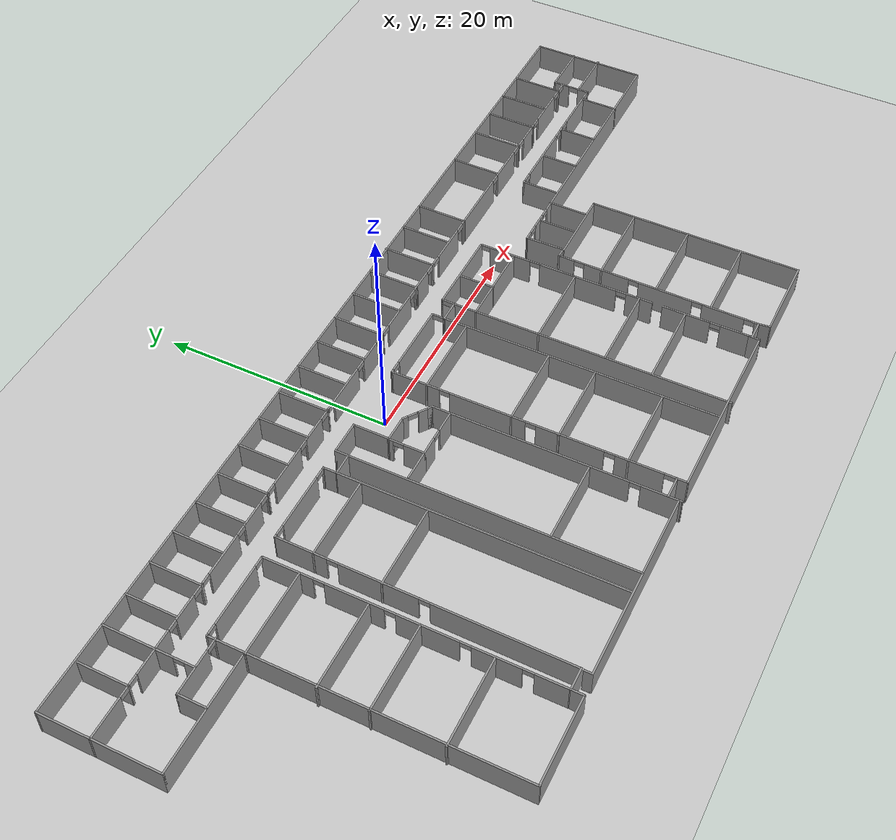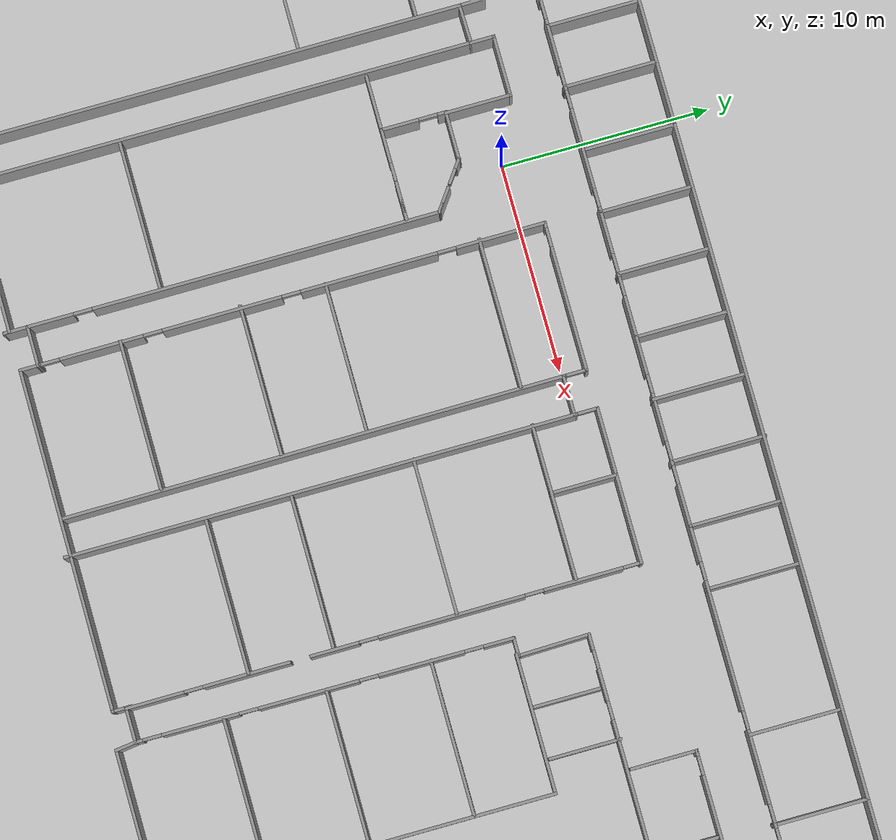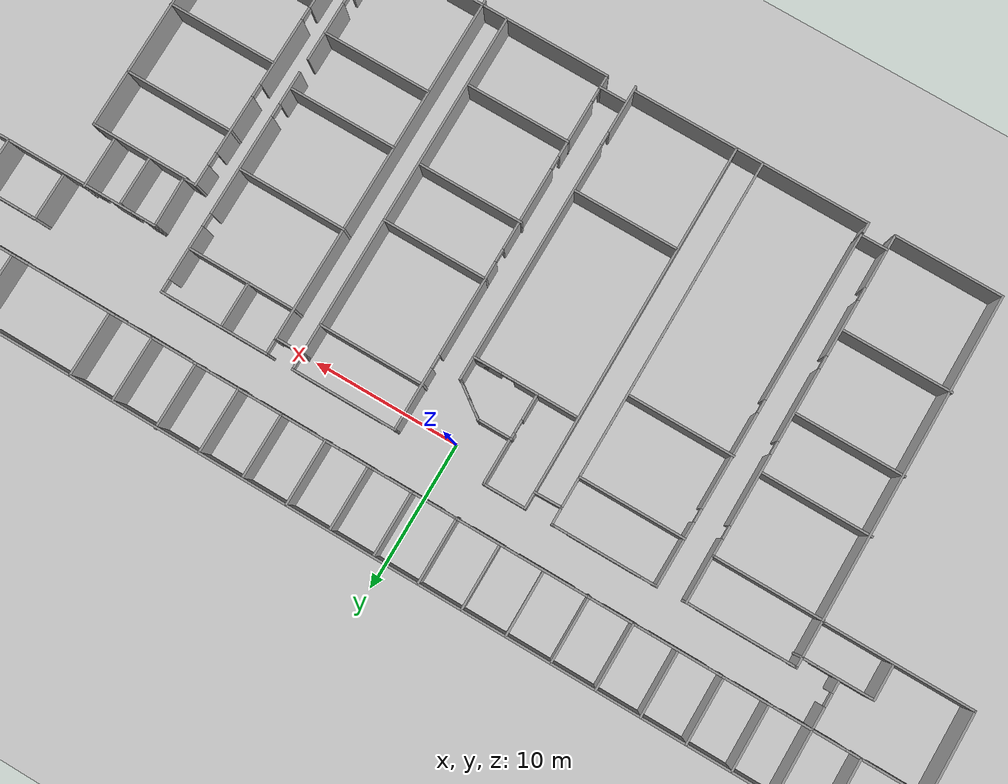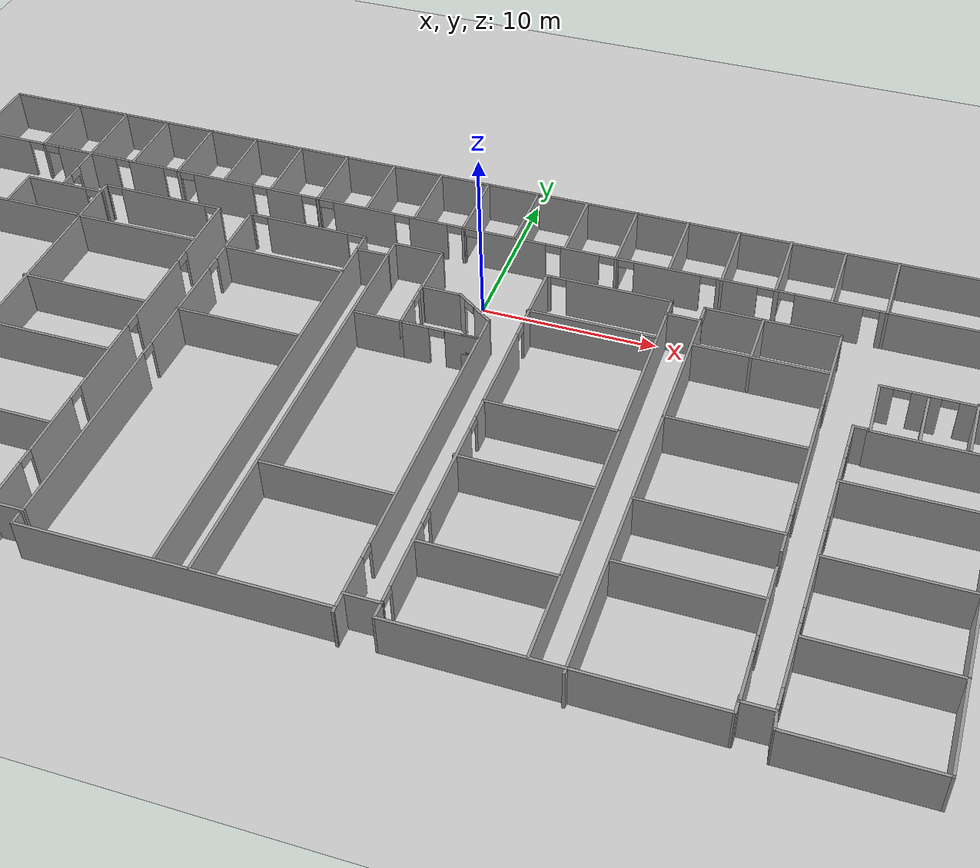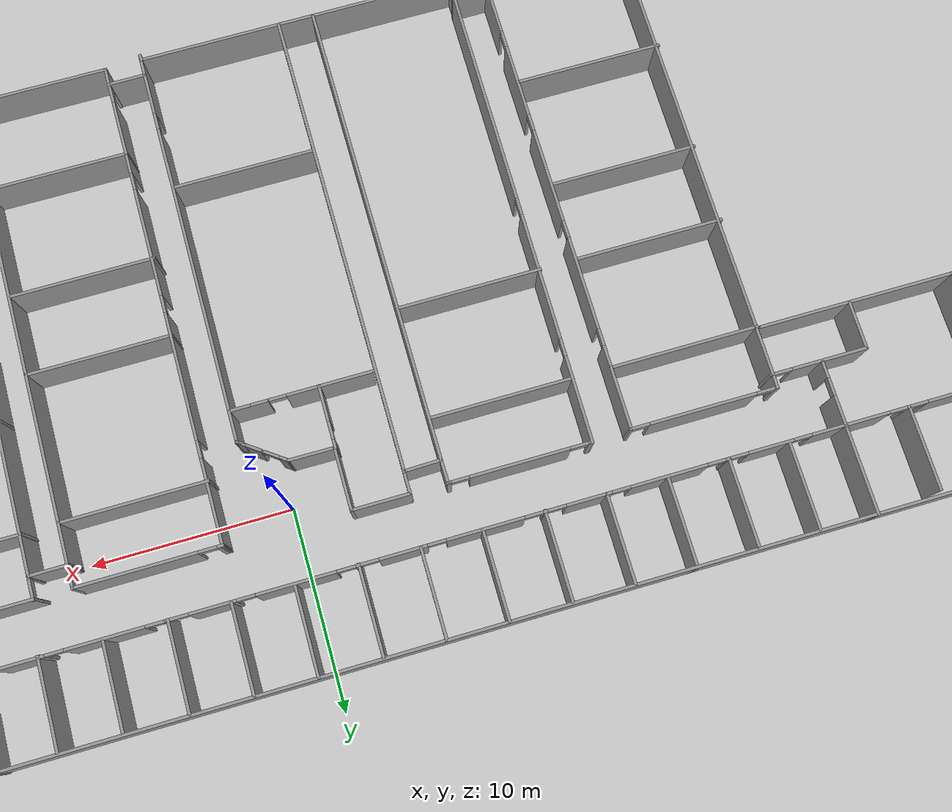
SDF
<sdf version="1.7">
 <world name="default">
  <light name="sun" type="directional">
   <pose>0 0 10 0 -0 0</pose>
   <diffuse>0.8 0.8 0.8 1</diffuse>
   <specular>0.2 0.2 0.2 1</specular>
   <attenuation>
    <range>1000</range>
    <constant>0.9</constant>
    <linear>0.01</linear>
    <quadratic>0.001</quadratic>
   </attenuation>
   <direction>-0.5 0.1 -0.9</direction>
   <spot><inner_angle>0</inner_angle><outer_angle>0</outer_angle><falloff>0</falloff></spot>
  </light>
  <model name="ground_plane">
   <static>1</static>
   <link name="link">
    <collision name="collision">
     <geometry><plane><normal>0 0 1</normal><size>100 100</size></plane></geometry>
     <surface><friction><ode><mu>100</mu><mu2>50</mu2></ode></friction></surface>
    </collision>
    <visual name="visual">
     <cast_shadows>0</cast_shadows>
     <geometry><plane><normal>0 0 1</normal><size>100 100</size></plane></geometry>
     <material>
      <script><uri>file://media/materials/scripts/gazebo.material</uri><name>Gazebo/Grey</name></script>
     </material>
    </visual>
   </link>
  </model>
  <gravity>0 0 -9.8</gravity>
  <magnetic_field>6e-06 2.3e-05 -4.2e-05</magnetic_field>
  <atmosphere type="adiabatic"/>
  <physics type="ode">
   <max_step_size>0.001</max_step_size>
   <real_time_factor>1</real_time_factor>
   <real_time_update_rate>1000</real_time_update_rate>
  </physics>
  <scene><ambient>0.4 0.4 0.4 1</ambient><background>0.7 0.7 0.7 1</background><shadows>1</shadows></scene>
  <audio><device>default</device></audio>
  <spherical_coordinates>
   <surface_model>EARTH_WGS84</surface_model>
   <latitude_deg>0</latitude_deg>
   <longitude_deg>0</longitude_deg>
   <elevation>0</elevation>
   <heading_deg>0</heading_deg>
  </spherical_coordinates>
  <model name="jec_6th_all_doors">
   <pose>6.89447 -8.09984 0 0 -0 0</pose>
   <link name="Wall_1">
    <collision name="Wall_1_Collision">
     <geometry><box><size>81.75 0.15 2.5</size></box></geometry>
     <pose>0 0 1.25 0 -0 0</pose>
    </collision>
    <visual name="Wall_1_Visual">
     <pose>0 0 1.25 0 -0 0</pose>
     <geometry><box><size>81.75 0.15 2.5</size></box></geometry>
     <material>
      <script><uri>file://media/materials/scripts/gazebo.material</uri><name>Gazebo/Grey</name></script>
      <ambient>1 1 1 1</ambient>
     </material>
     <meta><layer>0</layer></meta>
    </visual>
    <pose>-0.09521 16.2559 0 0 -0 0</pose>
   </link>
   <link name="Wall_10">
    <collision name="Wall_10_Collision">
     <geometry><box><size>1.75 0.15 2.5</size></box></geometry>
     <pose>0 0 1.25 0 -0 0</pose>
    </collision>
    <visual name="Wall_10_Visual">
     <pose>0 0 1.25 0 -0 0</pose>
     <geometry><box><size>1.75 0.15 2.5</size></box></geometry>
     <material>
      <script><uri>file://media/materials/scripts/gazebo.material</uri><name>Gazebo/Grey</name></script>
      <ambient>1 1 1 1</ambient>
     </material>
     <meta><layer>0</layer></meta>
    </visual>
    <pose>13.6994 -15.3577 0 0 -0 3.14159</pose>
   </link>
   <link name="Wall_100">
    <collision name="Wall_100_Collision">
     <geometry><box><size>4.5 0.15 2.5</size></box></geometry>
     <pose>0 0 1.25 0 -0 0</pose>
    </collision>
    <visual name="Wall_100_Visual">
     <pose>0 0 1.25 0 -0 0</pose>
     <geometry><box><size>4.5 0.15 2.5</size></box></geometry>
     <material>
      <script><uri>file://media/materials/scripts/gazebo.material</uri><name>Gazebo/Grey</name></script>
      <ambient>1 1 1 1</ambient>
     </material>
     <meta><layer>0</layer></meta>
    </visual>
    <pose>11.8384 14.0513 0 0 -0 1.5708</pose>
   </link>
   <link name="Wall_102">
    <collision name="Wall_102_Collision">
     <geometry><box><size>4.5 0.15 2.5</size></box></geometry>
     <pose>0 0 1.25 0 -0 0</pose>
    </collision>
    <visual name="Wall_102_Visual">
     <pose>0 0 1.25 0 -0 0</pose>
     <geometry><box><size>4.5 0.15 2.5</size></box></geometry>
     <material>
      <script><uri>file://media/materials/scripts/gazebo.material</uri><name>Gazebo/Grey</name></script>
      <ambient>1 1 1 1</ambient>
     </material>
     <meta><layer>0</layer></meta>
    </visual>
    <pose>14.8392 14.0233 0 0 -0 1.5708</pose>
   </link>
   <link name="Wall_104">
    <collision name="Wall_104_Collision">
     <geometry><box><size>4.5 0.15 2.5</size></box></geometry>
     <pose>0 0 1.25 0 -0 0</pose>
    </collision>
    <visual name="Wall_104_Visual">
     <pose>0 0 1.25 0 -0 0</pose>
     <geometry><box><size>4.5 0.15 2.5</size></box></geometry>
     <material>
      <script><uri>file://media/materials/scripts/gazebo.material</uri><name>Gazebo/Grey</name></script>
      <ambient>1 1 1 1</ambient>
     </material>
     <meta><layer>0</layer></meta>
    </visual>
    <pose>21.7944 14.0373 0 0 -0 1.5708</pose>
   </link>
   <link name="Wall_106">
    <collision name="Wall_106_Collision">
     <geometry><box><size>4.5 0.15 2.5</size></box></geometry>
     <pose>0 0 1.25 0 -0 0</pose>
    </collision>
    <visual name="Wall_106_Visual">
     <pose>0 0 1.25 0 -0 0</pose>
     <geometry><box><size>4.5 0.15 2.5</size></box></geometry>
     <material>
      <script><uri>file://media/materials/scripts/gazebo.material</uri><name>Gazebo/Grey</name></script>
      <ambient>1 1 1 1</ambient>
     </material>
     <meta><layer>0</layer></meta>
    </visual>
    <pose>26.0713 14.0093 0 0 -0 1.5708</pose>
   </link>
   <link name="Wall_108">
    <collision name="Wall_108_Collision">
     <geometry><box><size>4.5 0.15 2.5</size></box></geometry>
     <pose>0 0 1.25 0 -0 0</pose>
    </collision>
    <visual name="Wall_108_Visual">
     <pose>0 0 1.25 0 -0 0</pose>
     <geometry><box><size>4.5 0.15 2.5</size></box></geometry>
     <material>
      <script><uri>file://media/materials/scripts/gazebo.material</uri><name>Gazebo/Grey</name></script>
      <ambient>1 1 1 1</ambient>
     </material>
     <meta><layer>0</layer></meta>
    </visual>
    <pose>29.1282 13.9812 0 0 -0 1.5708</pose>
   </link>
   <link name="Wall_11">
    <pose>12.8709 -3.07187 0 0 -0 1.57311</pose>
    <visual name="Wall_11_Visual_0">
     <pose>-10.9495 0 1.25 0 -0 0</pose>
     <geometry><box><size>2.82258 0.15 2.5</size></box></geometry>
     <material>
      <script><uri>file://media/materials/scripts/gazebo.material</uri><name>Gazebo/Grey</name></script>
      <ambient>1 1 1 1</ambient>
     </material>
     <meta><layer>0</layer></meta>
    </visual>
    <collision name="Wall_11_Collision_0">
     <geometry><box><size>2.82258 0.15 2.5</size></box></geometry>
     <pose>-10.9495 0 1.25 0 -0 0</pose>
    </collision>
    <visual name="Wall_11_Visual_1">
     <pose>-6.5426 0 1.25 0 -0 0</pose>
     <geometry><box><size>4.19128 0.15 2.5</size></box></geometry>
     <material>
      <script><uri>file://media/materials/scripts/gazebo.material</uri><name>Gazebo/Grey</name></script>
      <ambient>1 1 1 1</ambient>
     </material>
     <meta><layer>0</layer></meta>
    </visual>
    <collision name="Wall_11_Collision_1">
     <geometry><box><size>4.19128 0.15 2.5</size></box></geometry>
     <pose>-6.5426 0 1.25 0 -0 0</pose>
    </collision>
    <visual name="Wall_11_Visual_2">
     <pose>-2.36845 0 1.25 0 -0 0</pose>
     <geometry><box><size>2.35702 0.15 2.5</size></box></geometry>
     <material>
      <script><uri>file://media/materials/scripts/gazebo.material</uri><name>Gazebo/Grey</name></script>
      <ambient>1 1 1 1</ambient>
     </material>
     <meta><layer>0</layer></meta>
    </visual>
    <collision name="Wall_11_Collision_2">
     <geometry><box><size>2.35702 0.15 2.5</size></box></geometry>
     <pose>-2.36845 0 1.25 0 -0 0</pose>
    </collision>
    <visual name="Wall_11_Visual_3">
     <pose>3.22052 0 1.25 0 -0 0</pose>
     <geometry><box><size>7.02092 0.15 2.5</size></box></geometry>
     <material>
      <script><uri>file://media/materials/scripts/gazebo.material</uri><name>Gazebo/Grey</name></script>
      <ambient>1 1 1 1</ambient>
     </material>
     <meta><layer>0</layer></meta>
    </visual>
    <collision name="Wall_11_Collision_3">
     <geometry><box><size>7.02092 0.15 2.5</size></box></geometry>
     <pose>3.22052 0 1.25 0 -0 0</pose>
    </collision>
    <visual name="Wall_11_Visual_4">
     <pose>9.5292 0 1.25 0 -0 0</pose>
     <geometry><box><size>3.79644 0.15 2.5</size></box></geometry>
     <material>
      <script><uri>file://media/materials/scripts/gazebo.material</uri><name>Gazebo/Grey</name></script>
      <ambient>1 1 1 1</ambient>
     </material>
     <meta><layer>0</layer></meta>
    </visual>
    <collision name="Wall_11_Collision_4">
     <geometry><box><size>3.79644 0.15 2.5</size></box></geometry>
     <pose>9.5292 0 1.25 0 -0 0</pose>
    </collision>
    <visual name="Wall_11_Visual_5">
     <pose>12.3441 0 1.25 0 -0 0</pose>
     <geometry><box><size>0.033401 0.15 2.5</size></box></geometry>
     <material>
      <script><uri>file://media/materials/scripts/gazebo.material</uri><name>Gazebo/Grey</name></script>
      <ambient>1 1 1 1</ambient>
     </material>
     <meta><layer>0</layer></meta>
    </visual>
    <collision name="Wall_11_Collision_5">
     <geometry><box><size>0.033401 0.15 2.5</size></box></geometry>
     <pose>12.3441 0 1.25 0 -0 0</pose>
    </collision>
    <visual name="Wall_11_Visual_6">
     <pose>-9.08824 0 2.25 0 -0 0</pose>
     <geometry><box><size>0.9 0.15 0.5</size></box></geometry>
     <material>
      <script><uri>file://media/materials/scripts/gazebo.material</uri><name>Gazebo/Grey</name></script>
      <ambient>1 1 1 1</ambient>
     </material>
     <meta><layer>0</layer></meta>
    </visual>
    <collision name="Wall_11_Collision_6">
     <geometry><box><size>0.9 0.15 0.5</size></box></geometry>
     <pose>-9.08824 0 2.25 0 -0 0</pose>
    </collision>
    <visual name="Wall_11_Visual_7">
     <pose>-4.44696 0 2.25 0 -0 0</pose>
     <geometry><box><size>0 0.15 0.5</size></box></geometry>
     <material>
      <script><uri>file://media/materials/scripts/gazebo.material</uri><name>Gazebo/Grey</name></script>
      <ambient>1 1 1 1</ambient>
     </material>
     <meta><layer>0</layer></meta>
    </visual>
    <collision name="Wall_11_Collision_7">
     <geometry><box><size>0 0.15 0.5</size></box></geometry>
     <pose>-4.44696 0 2.25 0 -0 0</pose>
    </collision>
    <visual name="Wall_11_Visual_8">
     <pose>-0.73994 0 2.25 0 -0 0</pose>
     <geometry><box><size>0.9 0.15 0.5</size></box></geometry>
     <material>
      <script><uri>file://media/materials/scripts/gazebo.material</uri><name>Gazebo/Grey</name></script>
      <ambient>1 1 1 1</ambient>
     </material>
     <meta><layer>0</layer></meta>
    </visual>
    <collision name="Wall_11_Collision_8">
     <geometry><box><size>0.9 0.15 0.5</size></box></geometry>
     <pose>-0.73994 0 2.25 0 -0 0</pose>
    </collision>
    <visual name="Wall_11_Visual_9">
     <pose>7.18098 0 2.25 0 -0 0</pose>
     <geometry><box><size>0.9 0.15 0.5</size></box></geometry>
     <material>
      <script><uri>file://media/materials/scripts/gazebo.material</uri><name>Gazebo/Grey</name></script>
      <ambient>1 1 1 1</ambient>
     </material>
     <meta><layer>0</layer></meta>
    </visual>
    <collision name="Wall_11_Collision_9">
     <geometry><box><size>0.9 0.15 0.5</size></box></geometry>
     <pose>7.18098 0 2.25 0 -0 0</pose>
    </collision>
    <visual name="Wall_11_Visual_10">
     <pose>11.8774 0 2.25 0 -0 0</pose>
     <geometry><box><size>0.9 0.15 0.5</size></box></geometry>
     <material>
      <script><uri>file://media/materials/scripts/gazebo.material</uri><name>Gazebo/Grey</name></script>
      <ambient>1 1 1 1</ambient>
     </material>
     <meta><layer>0</layer></meta>
    </visual>
    <collision name="Wall_11_Collision_10">
     <geometry><box><size>0.9 0.15 0.5</size></box></geometry>
     <pose>11.8774 0 2.25 0 -0 0</pose>
    </collision>
   </link>
   <link name="Wall_110">
    <collision name="Wall_110_Collision">
     <geometry><box><size>4.5 0.15 2.5</size></box></geometry>
     <pose>0 0 1.25 0 -0 0</pose>
    </collision>
    <visual name="Wall_110_Visual">
     <pose>0 0 1.25 0 -0 0</pose>
     <geometry><box><size>4.5 0.15 2.5</size></box></geometry>
     <material>
      <script><uri>file://media/materials/scripts/gazebo.material</uri><name>Gazebo/Grey</name></script>
      <ambient>1 1 1 1</ambient>
     </material>
     <meta><layer>0</layer></meta>
    </visual>
    <pose>32.0766 14.0631 0 0 -0 1.5708</pose>
   </link>
   <link name="Wall_112">
    <collision name="Wall_112_Collision">
     <geometry><box><size>4.5 0.15 2.5</size></box></geometry>
     <pose>0 0 1.25 0 -0 0</pose>
    </collision>
    <visual name="Wall_112_Visual">
     <pose>0 0 1.25 0 -0 0</pose>
     <geometry><box><size>4.5 0.15 2.5</size></box></geometry>
     <material>
      <script><uri>file://media/materials/scripts/gazebo.material</uri><name>Gazebo/Grey</name></script>
      <ambient>1 1 1 1</ambient>
     </material>
     <meta><layer>0</layer></meta>
    </visual>
    <pose>35.118 14.0631 0 0 -0 1.5708</pose>
   </link>
   <link name="Wall_114">
    <pose>-17.9306 9.30234 0 0 -0 0</pose>
    <visual name="Wall_114_Visual_0">
     <pose>-3.49815 0 1.25 0 -0 0</pose>
     <geometry><box><size>0.253703 0.15 2.5</size></box></geometry>
     <material>
      <script><uri>file://media/materials/scripts/gazebo.material</uri><name>Gazebo/Grey</name></script>
      <ambient>1 1 1 1</ambient>
     </material>
     <meta><layer>0</layer></meta>
    </visual>
    <collision name="Wall_114_Collision_0">
     <geometry><box><size>0.253703 0.15 2.5</size></box></geometry>
     <pose>-3.49815 0 1.25 0 -0 0</pose>
    </collision>
    <visual name="Wall_114_Visual_1">
     <pose>0.013816 0 1.25 0 -0 0</pose>
     <geometry><box><size>4.97023 0.15 2.5</size></box></geometry>
     <material>
      <script><uri>file://media/materials/scripts/gazebo.material</uri><name>Gazebo/Grey</name></script>
      <ambient>1 1 1 1</ambient>
     </material>
     <meta><layer>0</layer></meta>
    </visual>
    <collision name="Wall_114_Collision_1">
     <geometry><box><size>4.97023 0.15 2.5</size></box></geometry>
     <pose>0.013816 0 1.25 0 -0 0</pose>
    </collision>
    <visual name="Wall_114_Visual_2">
     <pose>3.51197 0 1.25 0 -0 0</pose>
     <geometry><box><size>0.22607 0.15 2.5</size></box></geometry>
     <material>
      <script><uri>file://media/materials/scripts/gazebo.material</uri><name>Gazebo/Grey</name></script>
      <ambient>1 1 1 1</ambient>
     </material>
     <meta><layer>0</layer></meta>
    </visual>
    <collision name="Wall_114_Collision_2">
     <geometry><box><size>0.22607 0.15 2.5</size></box></geometry>
     <pose>3.51197 0 1.25 0 -0 0</pose>
    </collision>
    <visual name="Wall_114_Visual_3">
     <pose>-2.9213 0 2.25 0 -0 0</pose>
     <geometry><box><size>0.9 0.15 0.5</size></box></geometry>
     <material>
      <script><uri>file://media/materials/scripts/gazebo.material</uri><name>Gazebo/Grey</name></script>
      <ambient>1 1 1 1</ambient>
     </material>
     <meta><layer>0</layer></meta>
    </visual>
    <collision name="Wall_114_Collision_3">
     <geometry><box><size>0.9 0.15 0.5</size></box></geometry>
     <pose>-2.9213 0 2.25 0 -0 0</pose>
    </collision>
    <visual name="Wall_114_Visual_4">
     <pose>2.94893 0 2.25 0 -0 0</pose>
     <geometry><box><size>0.9 0.15 0.5</size></box></geometry>
     <material>
      <script><uri>file://media/materials/scripts/gazebo.material</uri><name>Gazebo/Grey</name></script>
      <ambient>1 1 1 1</ambient>
     </material>
     <meta><layer>0</layer></meta>
    </visual>
    <collision name="Wall_114_Collision_4">
     <geometry><box><size>0.9 0.15 0.5</size></box></geometry>
     <pose>2.94893 0 2.25 0 -0 0</pose>
    </collision>
   </link>
   <link name="Wall_115">
    <collision name="Wall_115_Collision">
     <geometry><box><size>1.29228 0.15 2.5</size></box></geometry>
     <pose>0 0 1.25 0 -0 0</pose>
    </collision>
    <visual name="Wall_115_Visual">
     <pose>0 0 1.25 0 -0 0</pose>
     <geometry><box><size>1.29228 0.15 2.5</size></box></geometry>
     <material>
      <script><uri>file://media/materials/scripts/gazebo.material</uri><name>Gazebo/Grey</name></script>
      <ambient>1 1 1 1</ambient>
     </material>
     <meta><layer>0</layer></meta>
    </visual>
    <pose>-14.3714 8.72789 0 0 -0 -1.56045</pose>
   </link>
   <link name="Wall_116">
    <collision name="Wall_116_Collision">
     <geometry><box><size>1.98184 0.15 2.5</size></box></geometry>
     <pose>0 0 1.25 0 -0 0</pose>
    </collision>
    <visual name="Wall_116_Visual">
     <pose>0 0 1.25 0 -0 0</pose>
     <geometry><box><size>1.98184 0.15 2.5</size></box></geometry>
     <material>
      <script><uri>file://media/materials/scripts/gazebo.material</uri><name>Gazebo/Grey</name></script>
      <ambient>1 1 1 1</ambient>
     </material>
     <meta><layer>0</layer></meta>
    </visual>
    <pose>-13.4497 8.17381 0 0 -0 0.018591</pose>
   </link>
   <link name="Wall_117">
    <collision name="Wall_117_Collision">
     <geometry><box><size>1.25 0.15 2.5</size></box></geometry>
     <pose>0 0 1.25 0 -0 0</pose>
    </collision>
    <visual name="Wall_117_Visual">
     <pose>0 0 1.25 0 -0 0</pose>
     <geometry><box><size>1.25 0.15 2.5</size></box></geometry>
     <material>
      <script><uri>file://media/materials/scripts/gazebo.material</uri><name>Gazebo/Grey</name></script>
      <ambient>1 1 1 1</ambient>
     </material>
     <meta><layer>0</layer></meta>
    </visual>
    <pose>-12.5339 8.74083 0 0 -0 1.5708</pose>
   </link>
   <link name="Wall_118">
    <collision name="Wall_118_Collision">
     <geometry><box><size>3 0.15 2.5</size></box></geometry>
     <pose>0 0 1.25 0 -0 0</pose>
    </collision>
    <visual name="Wall_118_Visual">
     <pose>0 0 1.25 0 -0 0</pose>
     <geometry><box><size>3 0.15 2.5</size></box></geometry>
     <material>
      <script><uri>file://media/materials/scripts/gazebo.material</uri><name>Gazebo/Grey</name></script>
      <ambient>1 1 1 1</ambient>
     </material>
     <meta><layer>0</layer></meta>
    </visual>
    <pose>-11.1089 9.29083 0 0 -0 0</pose>
   </link>
   <link name="Wall_120">
    <pose>0.042504 9.21391 0 0 -0 0</pose>
    <visual name="Wall_120_Visual_0">
     <pose>-3.46085 0 1.25 0 -0 0</pose>
     <geometry><box><size>0.328296 0.15 2.5</size></box></geometry>
     <material>
      <script><uri>file://media/materials/scripts/gazebo.material</uri><name>Gazebo/Grey</name></script>
      <ambient>1 1 1 1</ambient>
     </material>
     <meta><layer>0</layer></meta>
    </visual>
    <collision name="Wall_120_Collision_0">
     <geometry><box><size>0.328296 0.15 2.5</size></box></geometry>
     <pose>-3.46085 0 1.25 0 -0 0</pose>
    </collision>
    <visual name="Wall_120_Visual_1">
     <pose>0.614148 0 1.25 0 -0 0</pose>
     <geometry><box><size>6.0217 0.15 2.5</size></box></geometry>
     <material>
      <script><uri>file://media/materials/scripts/gazebo.material</uri><name>Gazebo/Grey</name></script>
      <ambient>1 1 1 1</ambient>
     </material>
     <meta><layer>0</layer></meta>
    </visual>
    <collision name="Wall_120_Collision_1">
     <geometry><box><size>6.0217 0.15 2.5</size></box></geometry>
     <pose>0.614148 0 1.25 0 -0 0</pose>
    </collision>
    <visual name="Wall_120_Visual_2">
     <pose>-2.8467 0 2.25 0 -0 0</pose>
     <geometry><box><size>0.9 0.15 0.5</size></box></geometry>
     <material>
      <script><uri>file://media/materials/scripts/gazebo.material</uri><name>Gazebo/Grey</name></script>
      <ambient>1 1 1 1</ambient>
     </material>
     <meta><layer>0</layer></meta>
    </visual>
    <collision name="Wall_120_Collision_2">
     <geometry><box><size>0.9 0.15 0.5</size></box></geometry>
     <pose>-2.8467 0 2.25 0 -0 0</pose>
    </collision>
   </link>
   <link name="Wall_121">
    <pose>3.5925 8.66391 0 0 -0 -1.5708</pose>
    <visual name="Wall_121_Visual_0">
     <pose>-0.552987 0 1.25 0 -0 0</pose>
     <geometry><box><size>0.144027 0.15 2.5</size></box></geometry>
     <material>
      <script><uri>file://media/materials/scripts/gazebo.material</uri><name>Gazebo/Grey</name></script>
      <ambient>1 1 1 1</ambient>
     </material>
     <meta><layer>0</layer></meta>
    </visual>
    <collision name="Wall_121_Collision_0">
     <geometry><box><size>0.144027 0.15 2.5</size></box></geometry>
     <pose>-0.552987 0 1.25 0 -0 0</pose>
    </collision>
    <visual name="Wall_121_Visual_1">
     <pose>0.522013 0 1.25 0 -0 0</pose>
     <geometry><box><size>0.205973 0.15 2.5</size></box></geometry>
     <material>
      <script><uri>file://media/materials/scripts/gazebo.material</uri><name>Gazebo/Grey</name></script>
      <ambient>1 1 1 1</ambient>
     </material>
     <meta><layer>0</layer></meta>
    </visual>
    <collision name="Wall_121_Collision_1">
     <geometry><box><size>0.205973 0.15 2.5</size></box></geometry>
     <pose>0.522013 0 1.25 0 -0 0</pose>
    </collision>
    <visual name="Wall_121_Visual_2">
     <pose>-0.030973 0 2.25 0 -0 0</pose>
     <geometry><box><size>0.9 0.15 0.5</size></box></geometry>
     <material>
      <script><uri>file://media/materials/scripts/gazebo.material</uri><name>Gazebo/Grey</name></script>
      <ambient>1 1 1 1</ambient>
     </material>
     <meta><layer>0</layer></meta>
    </visual>
    <collision name="Wall_121_Collision_2">
     <geometry><box><size>0.9 0.15 0.5</size></box></geometry>
     <pose>-0.030973 0 2.25 0 -0 0</pose>
    </collision>
   </link>
   <link name="Wall_122">
    <collision name="Wall_122_Collision">
     <geometry><box><size>2 0.15 2.5</size></box></geometry>
     <pose>0 0 1.25 0 -0 0</pose>
    </collision>
    <visual name="Wall_122_Visual">
     <pose>0 0 1.25 0 -0 0</pose>
     <geometry><box><size>2 0.15 2.5</size></box></geometry>
     <material>
      <script><uri>file://media/materials/scripts/gazebo.material</uri><name>Gazebo/Grey</name></script>
      <ambient>1 1 1 1</ambient>
     </material>
     <meta><layer>0</layer></meta>
    </visual>
    <pose>4.5175 8.11391 0 0 -0 0</pose>
   </link>
   <link name="Wall_123">
    <pose>5.4425 8.66391 0 0 -0 1.5708</pose>
    <visual name="Wall_123_Visual_0">
     <pose>-0.514107 0 1.25 0 -0 0</pose>
     <geometry><box><size>0.221785 0.15 2.5</size></box></geometry>
     <material>
      <script><uri>file://media/materials/scripts/gazebo.material</uri><name>Gazebo/Grey</name></script>
      <ambient>1 1 1 1</ambient>
     </material>
     <meta><layer>0</layer></meta>
    </visual>
    <collision name="Wall_123_Collision_0">
     <geometry><box><size>0.221785 0.15 2.5</size></box></geometry>
     <pose>-0.514107 0 1.25 0 -0 0</pose>
    </collision>
    <visual name="Wall_123_Visual_1">
     <pose>0.560893 0 1.25 0 -0 0</pose>
     <geometry><box><size>0.128215 0.15 2.5</size></box></geometry>
     <material>
      <script><uri>file://media/materials/scripts/gazebo.material</uri><name>Gazebo/Grey</name></script>
      <ambient>1 1 1 1</ambient>
     </material>
     <meta><layer>0</layer></meta>
    </visual>
    <collision name="Wall_123_Collision_1">
     <geometry><box><size>0.128215 0.15 2.5</size></box></geometry>
     <pose>0.560893 0 1.25 0 -0 0</pose>
    </collision>
    <visual name="Wall_123_Visual_2">
     <pose>0.046785 0 2.25 0 -0 0</pose>
     <geometry><box><size>0.9 0.15 0.5</size></box></geometry>
     <material>
      <script><uri>file://media/materials/scripts/gazebo.material</uri><name>Gazebo/Grey</name></script>
      <ambient>1 1 1 1</ambient>
     </material>
     <meta><layer>0</layer></meta>
    </visual>
    <collision name="Wall_123_Collision_2">
     <geometry><box><size>0.9 0.15 0.5</size></box></geometry>
     <pose>0.046785 0 2.25 0 -0 0</pose>
    </collision>
   </link>
   <link name="Wall_124">
    <collision name="Wall_124_Collision">
     <geometry><box><size>7.55 0.15 2.5</size></box></geometry>
     <pose>0 0 1.25 0 -0 0</pose>
    </collision>
    <visual name="Wall_124_Visual">
     <pose>0 0 1.25 0 -0 0</pose>
     <geometry><box><size>7.55 0.15 2.5</size></box></geometry>
     <material>
      <script><uri>file://media/materials/scripts/gazebo.material</uri><name>Gazebo/Grey</name></script>
      <ambient>1 1 1 1</ambient>
     </material>
     <meta><layer>0</layer></meta>
    </visual>
    <pose>9.1425 9.21391 0 0 -0 0</pose>
   </link>
   <link name="Wall_127">
    <collision name="Wall_127_Collision">
     <geometry><box><size>24.5 0.15 2.5</size></box></geometry>
     <pose>0 0 1.25 0 -0 0</pose>
    </collision>
    <visual name="Wall_127_Visual">
     <pose>0 0 1.25 0 -0 0</pose>
     <geometry><box><size>24.5 0.15 2.5</size></box></geometry>
     <material>
      <script><uri>file://media/materials/scripts/gazebo.material</uri><name>Gazebo/Grey</name></script>
      <ambient>1 1 1 1</ambient>
     </material>
     <meta><layer>0</layer></meta>
    </visual>
    <pose>5.4425 -4.06109 0 0 -0 -1.5708</pose>
   </link>
   <link name="Wall_129">
    <collision name="Wall_129_Collision">
     <geometry><box><size>7.5 0.15 2.5</size></box></geometry>
     <pose>0 0 1.25 0 -0 0</pose>
    </collision>
    <visual name="Wall_129_Visual">
     <pose>0 0 1.25 0 -0 0</pose>
     <geometry><box><size>7.5 0.15 2.5</size></box></geometry>
     <material>
      <script><uri>file://media/materials/scripts/gazebo.material</uri><name>Gazebo/Grey</name></script>
      <ambient>1 1 1 1</ambient>
     </material>
     <meta><layer>0</layer></meta>
    </visual>
    <pose>9.0767 6.11565 0 0 -0 0</pose>
   </link>
   <link name="Wall_13">
    <pose>-3.47906 -2.94687 0 0 -0 -1.56846</pose>
    <visual name="Wall_13_Visual_0">
     <pose>-10.0663 0 1.25 0 -0 0</pose>
     <geometry><box><size>4.33904 0.15 2.5</size></box></geometry>
     <material>
      <script><uri>file://media/materials/scripts/gazebo.material</uri><name>Gazebo/Grey</name></script>
      <ambient>1 1 1 1</ambient>
     </material>
     <meta><layer>0</layer></meta>
    </visual>
    <collision name="Wall_13_Collision_0">
     <geometry><box><size>4.33904 0.15 2.5</size></box></geometry>
     <pose>-10.0663 0 1.25 0 -0 0</pose>
    </collision>
    <visual name="Wall_13_Visual_1">
     <pose>-3.70749 0 1.25 0 -0 0</pose>
     <geometry><box><size>6.57857 0.15 2.5</size></box></geometry>
     <material>
      <script><uri>file://media/materials/scripts/gazebo.material</uri><name>Gazebo/Grey</name></script>
      <ambient>1 1 1 1</ambient>
     </material>
     <meta><layer>0</layer></meta>
    </visual>
    <collision name="Wall_13_Collision_1">
     <geometry><box><size>6.57857 0.15 2.5</size></box></geometry>
     <pose>-3.70749 0 1.25 0 -0 0</pose>
    </collision>
    <visual name="Wall_13_Visual_2">
     <pose>3.34972 0 1.25 0 -0 0</pose>
     <geometry><box><size>5.73586 0.15 2.5</size></box></geometry>
     <material>
      <script><uri>file://media/materials/scripts/gazebo.material</uri><name>Gazebo/Grey</name></script>
      <ambient>1 1 1 1</ambient>
     </material>
     <meta><layer>0</layer></meta>
    </visual>
    <collision name="Wall_13_Collision_2">
     <geometry><box><size>5.73586 0.15 2.5</size></box></geometry>
     <pose>3.34972 0 1.25 0 -0 0</pose>
    </collision>
    <visual name="Wall_13_Visual_3">
     <pose>9.12657 0 1.25 0 -0 0</pose>
     <geometry><box><size>4.01783 0.15 2.5</size></box></geometry>
     <material>
      <script><uri>file://media/materials/scripts/gazebo.material</uri><name>Gazebo/Grey</name></script>
      <ambient>1 1 1 1</ambient>
     </material>
     <meta><layer>0</layer></meta>
    </visual>
    <collision name="Wall_13_Collision_3">
     <geometry><box><size>4.01783 0.15 2.5</size></box></geometry>
     <pose>9.12657 0 1.25 0 -0 0</pose>
    </collision>
    <visual name="Wall_13_Visual_4">
     <pose>12.1357 0 1.25 0 -0 0</pose>
     <geometry><box><size>0.200326 0.15 2.5</size></box></geometry>
     <material>
      <script><uri>file://media/materials/scripts/gazebo.material</uri><name>Gazebo/Grey</name></script>
      <ambient>1 1 1 1</ambient>
     </material>
     <meta><layer>0</layer></meta>
    </visual>
    <collision name="Wall_13_Collision_4">
     <geometry><box><size>0.200326 0.15 2.5</size></box></geometry>
     <pose>12.1357 0 1.25 0 -0 0</pose>
    </collision>
    <visual name="Wall_13_Visual_5">
     <pose>-7.44677 0 2.25 0 -0 0</pose>
     <geometry><box><size>0.9 0.15 0.5</size></box></geometry>
     <material>
      <script><uri>file://media/materials/scripts/gazebo.material</uri><name>Gazebo/Grey</name></script>
      <ambient>1 1 1 1</ambient>
     </material>
     <meta><layer>0</layer></meta>
    </visual>
    <collision name="Wall_13_Collision_5">
     <geometry><box><size>0.9 0.15 0.5</size></box></geometry>
     <pose>-7.44677 0 2.25 0 -0 0</pose>
    </collision>
    <visual name="Wall_13_Visual_6">
     <pose>0.031795 0 2.25 0 -0 0</pose>
     <geometry><box><size>0.9 0.15 0.5</size></box></geometry>
     <material>
      <script><uri>file://media/materials/scripts/gazebo.material</uri><name>Gazebo/Grey</name></script>
      <ambient>1 1 1 1</ambient>
     </material>
     <meta><layer>0</layer></meta>
    </visual>
    <collision name="Wall_13_Collision_6">
     <geometry><box><size>0.9 0.15 0.5</size></box></geometry>
     <pose>0.031795 0 2.25 0 -0 0</pose>
    </collision>
    <visual name="Wall_13_Visual_7">
     <pose>6.66765 0 2.25 0 -0 0</pose>
     <geometry><box><size>0.9 0.15 0.5</size></box></geometry>
     <material>
      <script><uri>file://media/materials/scripts/gazebo.material</uri><name>Gazebo/Grey</name></script>
      <ambient>1 1 1 1</ambient>
     </material>
     <meta><layer>0</layer></meta>
    </visual>
    <collision name="Wall_13_Collision_7">
     <geometry><box><size>0.9 0.15 0.5</size></box></geometry>
     <pose>6.66765 0 2.25 0 -0 0</pose>
    </collision>
    <visual name="Wall_13_Visual_8">
     <pose>11.5855 0 2.25 0 -0 0</pose>
     <geometry><box><size>0.9 0.15 0.5</size></box></geometry>
     <material>
      <script><uri>file://media/materials/scripts/gazebo.material</uri><name>Gazebo/Grey</name></script>
      <ambient>1 1 1 1</ambient>
     </material>
     <meta><layer>0</layer></meta>
    </visual>
    <collision name="Wall_13_Collision_8">
     <geometry><box><size>0.9 0.15 0.5</size></box></geometry>
     <pose>11.5855 0 2.25 0 -0 0</pose>
    </collision>
   </link>
   <link name="Wall_131">
    <collision name="Wall_131_Collision">
     <geometry><box><size>3.25 0.15 2.5</size></box></geometry>
     <pose>0 0 1.25 0 -0 0</pose>
    </collision>
    <visual name="Wall_131_Visual">
     <pose>0 0 1.25 0 -0 0</pose>
     <geometry><box><size>3.25 0.15 2.5</size></box></geometry>
     <material>
      <script><uri>file://media/materials/scripts/gazebo.material</uri><name>Gazebo/Grey</name></script>
      <ambient>1 1 1 1</ambient>
     </material>
     <meta><layer>0</layer></meta>
    </visual>
    <pose>8.64352 7.65948 0 0 -0 -1.5708</pose>
   </link>
   <link name="Wall_133">
    <collision name="Wall_133_Collision">
     <geometry><box><size>7.5 0.15 2.5</size></box></geometry>
     <pose>0 0 1.25 0 -0 0</pose>
    </collision>
    <visual name="Wall_133_Visual">
     <pose>0 0 1.25 0 -0 0</pose>
     <geometry><box><size>7.5 0.15 2.5</size></box></geometry>
     <material>
      <script><uri>file://media/materials/scripts/gazebo.material</uri><name>Gazebo/Grey</name></script>
      <ambient>1 1 1 1</ambient>
     </material>
     <meta><layer>0</layer></meta>
    </visual>
    <pose>9.10958 0.409886 0 0 -0 0</pose>
   </link>
   <link name="Wall_135">
    <collision name="Wall_135_Collision">
     <geometry><box><size>7.5 0.15 2.5</size></box></geometry>
     <pose>0 0 1.25 0 -0 0</pose>
    </collision>
    <visual name="Wall_135_Visual">
     <pose>0 0 1.25 0 -0 0</pose>
     <geometry><box><size>7.5 0.15 2.5</size></box></geometry>
     <material>
      <script><uri>file://media/materials/scripts/gazebo.material</uri><name>Gazebo/Grey</name></script>
      <ambient>1 1 1 1</ambient>
     </material>
     <meta><layer>0</layer></meta>
    </visual>
    <pose>18.2355 -1.31664 0 0 -0 0</pose>
   </link>
   <link name="Wall_137">
    <collision name="Wall_137_Collision">
     <geometry><box><size>7.5 0.15 2.5</size></box></geometry>
     <pose>0 0 1.25 0 -0 0</pose>
    </collision>
    <visual name="Wall_137_Visual">
     <pose>0 0 1.25 0 -0 0</pose>
     <geometry><box><size>7.5 0.15 2.5</size></box></geometry>
     <material>
      <script><uri>file://media/materials/scripts/gazebo.material</uri><name>Gazebo/Grey</name></script>
      <ambient>1 1 1 1</ambient>
     </material>
     <meta><layer>0</layer></meta>
    </visual>
    <pose>18.3177 -6.29891 0 0 -0 0</pose>
   </link>
   <link name="Wall_139">
    <collision name="Wall_139_Collision">
     <geometry><box><size>7.5 0.15 2.5</size></box></geometry>
     <pose>0 0 1.25 0 -0 0</pose>
    </collision>
    <visual name="Wall_139_Visual">
     <pose>0 0 1.25 0 -0 0</pose>
     <geometry><box><size>7.5 0.15 2.5</size></box></geometry>
     <material>
      <script><uri>file://media/materials/scripts/gazebo.material</uri><name>Gazebo/Grey</name></script>
      <ambient>1 1 1 1</ambient>
     </material>
     <meta><layer>0</layer></meta>
    </visual>
    <pose>18.3056 -11.1696 0 0 -0 0</pose>
   </link>
   <link name="Wall_14">
    <collision name="Wall_14_Collision">
     <geometry><box><size>2 0.15 2.5</size></box></geometry>
     <pose>0 0 1.25 0 -0 0</pose>
    </collision>
    <visual name="Wall_14_Visual">
     <pose>0 0 1.25 0 -0 0</pose>
     <geometry><box><size>2 0.15 2.5</size></box></geometry>
     <material>
      <script><uri>file://media/materials/scripts/gazebo.material</uri><name>Gazebo/Grey</name></script>
      <ambient>1 1 1 1</ambient>
     </material>
     <meta><layer>0</layer></meta>
    </visual>
    <pose>-4.37563 -15.1077 0 0 -0 3.14159</pose>
   </link>
   <link name="Wall_141">
    <collision name="Wall_141_Collision">
     <geometry><box><size>1.10155 0.15 2.5</size></box></geometry>
     <pose>0 0 1.25 0 -0 0</pose>
    </collision>
    <visual name="Wall_141_Visual">
     <pose>0 0 1.25 0 -0 0</pose>
     <geometry><box><size>1.10155 0.15 2.5</size></box></geometry>
     <material>
      <script><uri>file://media/materials/scripts/gazebo.material</uri><name>Gazebo/Grey</name></script>
      <ambient>1 1 1 1</ambient>
     </material>
     <meta><layer>0</layer></meta>
    </visual>
    <pose>14.5593 -15.8296 0 0 -0 1.69711</pose>
   </link>
   <link name="Wall_143">
    <collision name="Wall_143_Collision">
     <geometry><box><size>7.5 0.15 2.5</size></box></geometry>
     <pose>0 0 1.25 0 -0 0</pose>
    </collision>
    <visual name="Wall_143_Visual">
     <pose>0 0 1.25 0 -0 0</pose>
     <geometry><box><size>7.5 0.15 2.5</size></box></geometry>
     <material>
      <script><uri>file://media/materials/scripts/gazebo.material</uri><name>Gazebo/Grey</name></script>
      <ambient>1 1 1 1</ambient>
     </material>
     <meta><layer>0</layer></meta>
    </visual>
    <pose>18.2942 -16.3016 0 0 -0 0</pose>
   </link>
   <link name="Wall_144">
    <collision name="Wall_144_Collision">
     <geometry><box><size>19 0.15 2.5</size></box></geometry>
     <pose>0 0 1.25 0 -0 0</pose>
    </collision>
    <visual name="Wall_144_Visual">
     <pose>0 0 1.25 0 -0 0</pose>
     <geometry><box><size>19 0.15 2.5</size></box></geometry>
     <material>
      <script><uri>file://media/materials/scripts/gazebo.material</uri><name>Gazebo/Grey</name></script>
      <ambient>1 1 1 1</ambient>
     </material>
     <meta><layer>0</layer></meta>
    </visual>
    <pose>21.9692 -6.87663 0 0 -0 1.5708</pose>
   </link>
   <link name="Wall_146">
    <collision name="Wall_146_Collision">
     <geometry><box><size>6.75 0.15 2.5</size></box></geometry>
     <pose>0 0 1.25 0 -0 0</pose>
    </collision>
    <visual name="Wall_146_Visual">
     <pose>0 0 1.25 0 -0 0</pose>
     <geometry><box><size>6.75 0.15 2.5</size></box></geometry>
     <material>
      <script><uri>file://media/materials/scripts/gazebo.material</uri><name>Gazebo/Grey</name></script>
      <ambient>1 1 1 1</ambient>
     </material>
     <meta><layer>0</layer></meta>
    </visual>
    <pose>18.6692 2.54837 0 0 -0 3.14159</pose>
   </link>
   <link name="Wall_148">
    <collision name="Wall_148_Collision">
     <geometry><box><size>3.5 0.15 2.5</size></box></geometry>
     <pose>0 0 1.25 0 -0 0</pose>
    </collision>
    <visual name="Wall_148_Visual">
     <pose>0 0 1.25 0 -0 0</pose>
     <geometry><box><size>3.5 0.15 2.5</size></box></geometry>
     <material>
      <script><uri>file://media/materials/scripts/gazebo.material</uri><name>Gazebo/Grey</name></script>
      <ambient>1 1 1 1</ambient>
     </material>
     <meta><layer>0</layer></meta>
    </visual>
    <pose>20.3752 4.41514 0 0 -0 -1.5708</pose>
   </link>
   <link name="Wall_150">
    <collision name="Wall_150_Collision">
     <geometry><box><size>7.5 0.15 2.5</size></box></geometry>
     <pose>0 0 1.25 0 -0 0</pose>
    </collision>
    <visual name="Wall_150_Visual">
     <pose>0 0 1.25 0 -0 0</pose>
     <geometry><box><size>7.5 0.15 2.5</size></box></geometry>
     <material>
      <script><uri>file://media/materials/scripts/gazebo.material</uri><name>Gazebo/Grey</name></script>
      <ambient>1 1 1 1</ambient>
     </material>
     <meta><layer>0</layer></meta>
    </visual>
    <pose>9.18576 -5.46599 0 0 -0 0</pose>
   </link>
   <link name="Wall_152">
    <collision name="Wall_152_Collision">
     <geometry><box><size>7.5 0.15 2.5</size></box></geometry>
     <pose>0 0 1.25 0 -0 0</pose>
    </collision>
    <visual name="Wall_152_Visual">
     <pose>0 0 1.25 0 -0 0</pose>
     <geometry><box><size>7.5 0.15 2.5</size></box></geometry>
     <material>
      <script><uri>file://media/materials/scripts/gazebo.material</uri><name>Gazebo/Grey</name></script>
      <ambient>1 1 1 1</ambient>
     </material>
     <meta><layer>0</layer></meta>
    </visual>
    <pose>9.17245 -9.53865 0 0 -0 0</pose>
   </link>
   <link name="Wall_154">
    <collision name="Wall_154_Collision">
     <geometry><box><size>24.1463 0.15 2.5</size></box></geometry>
     <pose>0 0 1.25 0 -0 0</pose>
    </collision>
    <visual name="Wall_154_Visual">
     <pose>0 0 1.25 0 -0 0</pose>
     <geometry><box><size>24.1463 0.15 2.5</size></box></geometry>
     <material>
      <script><uri>file://media/materials/scripts/gazebo.material</uri><name>Gazebo/Grey</name></script>
      <ambient>1 1 1 1</ambient>
     </material>
     <meta><layer>0</layer></meta>
    </visual>
    <pose>3.64282 -3.88413 0 0 -0 1.57499</pose>
   </link>
   <link name="Wall_156">
    <collision name="Wall_156_Collision">
     <geometry><box><size>7.25 0.15 2.5</size></box></geometry>
     <pose>0 0 1.25 0 -0 0</pose>
    </collision>
    <visual name="Wall_156_Visual">
     <pose>0 0 1.25 0 -0 0</pose>
     <geometry><box><size>7.25 0.15 2.5</size></box></geometry>
     <material>
      <script><uri>file://media/materials/scripts/gazebo.material</uri><name>Gazebo/Grey</name></script>
      <ambient>1 1 1 1</ambient>
     </material>
     <meta><layer>0</layer></meta>
    </visual>
    <pose>-0.017609 6.083 0 0 -0 0</pose>
   </link>
   <link name="Wall_158">
    <collision name="Wall_158_Collision">
     <geometry><box><size>7.25 0.15 2.5</size></box></geometry>
     <pose>0 0 1.25 0 -0 0</pose>
    </collision>
    <visual name="Wall_158_Visual">
     <pose>0 0 1.25 0 -0 0</pose>
     <geometry><box><size>7.25 0.15 2.5</size></box></geometry>
     <material>
      <script><uri>file://media/materials/scripts/gazebo.material</uri><name>Gazebo/Grey</name></script>
      <ambient>1 1 1 1</ambient>
     </material>
     <meta><layer>0</layer></meta>
    </visual>
    <pose>0.052917 -1.32219 0 0 -0 0</pose>
   </link>
   <link name="Wall_160">
    <collision name="Wall_160_Collision">
     <geometry><box><size>7.25 0.15 2.5</size></box></geometry>
     <pose>0 0 1.25 0 -0 0</pose>
    </collision>
    <visual name="Wall_160_Visual">
     <pose>0 0 1.25 0 -0 0</pose>
     <geometry><box><size>7.25 0.15 2.5</size></box></geometry>
     <material>
      <script><uri>file://media/materials/scripts/gazebo.material</uri><name>Gazebo/Grey</name></script>
      <ambient>1 1 1 1</ambient>
     </material>
     <meta><layer>0</layer></meta>
    </visual>
    <pose>-0.017609 -5.39505 0 0 -0 0</pose>
   </link>
   <link name="Wall_162">
    <collision name="Wall_162_Collision">
     <geometry><box><size>7.25 0.15 2.5</size></box></geometry>
     <pose>0 0 1.25 0 -0 0</pose>
    </collision>
    <visual name="Wall_162_Visual">
     <pose>0 0 1.25 0 -0 0</pose>
     <geometry><box><size>7.25 0.15 2.5</size></box></geometry>
     <material>
      <script><uri>file://media/materials/scripts/gazebo.material</uri><name>Gazebo/Grey</name></script>
      <ambient>1 1 1 1</ambient>
     </material>
     <meta><layer>0</layer></meta>
    </visual>
    <pose>0.070548 -11.1605 0 0 -0 0</pose>
   </link>
   <link name="Wall_164">
    <collision name="Wall_164_Collision">
     <geometry><box><size>24.25 0.15 2.5</size></box></geometry>
     <pose>0 0 1.25 0 -0 0</pose>
    </collision>
    <visual name="Wall_164_Visual">
     <pose>0 0 1.25 0 -0 0</pose>
     <geometry><box><size>24.25 0.15 2.5</size></box></geometry>
     <material>
      <script><uri>file://media/materials/scripts/gazebo.material</uri><name>Gazebo/Grey</name></script>
      <ambient>1 1 1 1</ambient>
     </material>
     <meta><layer>0</layer></meta>
    </visual>
    <pose>-12.542 -3.871 0 0 -0 1.5708</pose>
   </link>
   <link name="Wall_166">
    <collision name="Wall_166_Collision">
     <geometry><box><size>24.25 0.15 2.5</size></box></geometry>
     <pose>0 0 1.25 0 -0 0</pose>
    </collision>
    <visual name="Wall_166_Visual">
     <pose>0 0 1.25 0 -0 0</pose>
     <geometry><box><size>24.25 0.15 2.5</size></box></geometry>
     <material>
      <script><uri>file://media/materials/scripts/gazebo.material</uri><name>Gazebo/Grey</name></script>
      <ambient>1 1 1 1</ambient>
     </material>
     <meta><layer>0</layer></meta>
    </visual>
    <pose>-14.3655 -3.89322 0 0 -0 -1.5708</pose>
   </link>
   <link name="Wall_168">
    <collision name="Wall_168_Collision">
     <geometry><box><size>7.25 0.15 2.5</size></box></geometry>
     <pose>0 0 1.25 0 -0 0</pose>
    </collision>
    <visual name="Wall_168_Visual">
     <pose>0 0 1.25 0 -0 0</pose>
     <geometry><box><size>7.25 0.15 2.5</size></box></geometry>
     <material>
      <script><uri>file://media/materials/scripts/gazebo.material</uri><name>Gazebo/Grey</name></script>
      <ambient>1 1 1 1</ambient>
     </material>
     <meta><layer>0</layer></meta>
    </visual>
    <pose>-18.0458 0.388789 0 0 -0 0</pose>
   </link>
   <link name="Wall_17">
    <pose>-21.5623 -2.90601 0 0 -0 -1.57748</pose>
    <visual name="Wall_17_Visual_0">
     <pose>-10.0629 0 1.25 0 -0 0</pose>
     <geometry><box><size>4.44153 0.15 2.5</size></box></geometry>
     <material>
      <script><uri>file://media/materials/scripts/gazebo.material</uri><name>Gazebo/Grey</name></script>
      <ambient>1 1 1 1</ambient>
     </material>
     <meta><layer>0</layer></meta>
    </visual>
    <collision name="Wall_17_Collision_0">
     <geometry><box><size>4.44153 0.15 2.5</size></box></geometry>
     <pose>-10.0629 0 1.25 0 -0 0</pose>
    </collision>
    <visual name="Wall_17_Visual_1">
     <pose>-3.63692 0 1.25 0 -0 0</pose>
     <geometry><box><size>6.61036 0.15 2.5</size></box></geometry>
     <material>
      <script><uri>file://media/materials/scripts/gazebo.material</uri><name>Gazebo/Grey</name></script>
      <ambient>1 1 1 1</ambient>
     </material>
     <meta><layer>0</layer></meta>
    </visual>
    <collision name="Wall_17_Collision_1">
     <geometry><box><size>6.61036 0.15 2.5</size></box></geometry>
     <pose>-3.63692 0 1.25 0 -0 0</pose>
    </collision>
    <visual name="Wall_17_Visual_2">
     <pose>6.42594 0 1.25 0 -0 0</pose>
     <geometry><box><size>11.7154 0.15 2.5</size></box></geometry>
     <material>
      <script><uri>file://media/materials/scripts/gazebo.material</uri><name>Gazebo/Grey</name></script>
      <ambient>1 1 1 1</ambient>
     </material>
     <meta><layer>0</layer></meta>
    </visual>
    <collision name="Wall_17_Collision_2">
     <geometry><box><size>11.7154 0.15 2.5</size></box></geometry>
     <pose>6.42594 0 1.25 0 -0 0</pose>
    </collision>
    <visual name="Wall_17_Visual_3">
     <pose>-7.39209 0 2.25 0 -0 0</pose>
     <geometry><box><size>0.9 0.15 0.5</size></box></geometry>
     <material>
      <script><uri>file://media/materials/scripts/gazebo.material</uri><name>Gazebo/Grey</name></script>
      <ambient>1 1 1 1</ambient>
     </material>
     <meta><layer>0</layer></meta>
    </visual>
    <collision name="Wall_17_Collision_3">
     <geometry><box><size>0.9 0.15 0.5</size></box></geometry>
     <pose>-7.39209 0 2.25 0 -0 0</pose>
    </collision>
    <visual name="Wall_17_Visual_4">
     <pose>0.118263 0 2.25 0 -0 0</pose>
     <geometry><box><size>0.9 0.15 0.5</size></box></geometry>
     <material>
      <script><uri>file://media/materials/scripts/gazebo.material</uri><name>Gazebo/Grey</name></script>
      <ambient>1 1 1 1</ambient>
     </material>
     <meta><layer>0</layer></meta>
    </visual>
    <collision name="Wall_17_Collision_4">
     <geometry><box><size>0.9 0.15 0.5</size></box></geometry>
     <pose>0.118263 0 2.25 0 -0 0</pose>
    </collision>
   </link>
   <link name="Wall_170">
    <collision name="Wall_170_Collision">
     <geometry><box><size>7.25 0.15 2.5</size></box></geometry>
     <pose>0 0 1.25 0 -0 0</pose>
    </collision>
    <visual name="Wall_170_Visual">
     <pose>0 0 1.25 0 -0 0</pose>
     <geometry><box><size>7.25 0.15 2.5</size></box></geometry>
     <material>
      <script><uri>file://media/materials/scripts/gazebo.material</uri><name>Gazebo/Grey</name></script>
      <ambient>1 1 1 1</ambient>
     </material>
     <meta><layer>0</layer></meta>
    </visual>
    <pose>-17.962 6.0697 0 0 -0 0</pose>
   </link>
   <link name="Wall_172">
    <collision name="Wall_172_Collision">
     <geometry><box><size>7.5 0.15 2.5</size></box></geometry>
     <pose>0 0 1.25 0 -0 0</pose>
    </collision>
    <visual name="Wall_172_Visual">
     <pose>0 0 1.25 0 -0 0</pose>
     <geometry><box><size>7.5 0.15 2.5</size></box></geometry>
     <material>
      <script><uri>file://media/materials/scripts/gazebo.material</uri><name>Gazebo/Grey</name></script>
      <ambient>1 1 1 1</ambient>
     </material>
     <meta><layer>0</layer></meta>
    </visual>
    <pose>-27.1444 6.0861 0 0 -0 0</pose>
   </link>
   <link name="Wall_174">
    <collision name="Wall_174_Collision">
     <geometry><box><size>7.5 0.15 2.5</size></box></geometry>
     <pose>0 0 1.25 0 -0 0</pose>
    </collision>
    <visual name="Wall_174_Visual">
     <pose>0 0 1.25 0 -0 0</pose>
     <geometry><box><size>7.5 0.15 2.5</size></box></geometry>
     <material>
      <script><uri>file://media/materials/scripts/gazebo.material</uri><name>Gazebo/Grey</name></script>
      <ambient>1 1 1 1</ambient>
     </material>
     <meta><layer>0</layer></meta>
    </visual>
    <pose>-27.2593 0.386482 0 0 -0 0</pose>
   </link>
   <link name="Wall_176">
    <collision name="Wall_176_Collision">
     <geometry><box><size>7.5 0.15 2.5</size></box></geometry>
     <pose>0 0 1.25 0 -0 0</pose>
    </collision>
    <visual name="Wall_176_Visual">
     <pose>0 0 1.25 0 -0 0</pose>
     <geometry><box><size>7.5 0.15 2.5</size></box></geometry>
     <material>
      <script><uri>file://media/materials/scripts/gazebo.material</uri><name>Gazebo/Grey</name></script>
      <ambient>1 1 1 1</ambient>
     </material>
     <meta><layer>0</layer></meta>
    </visual>
    <pose>-27.2178 -3.68884 0 0 -0 0</pose>
   </link>
   <link name="Wall_178">
    <collision name="Wall_178_Collision">
     <geometry><box><size>7.5 0.15 2.5</size></box></geometry>
     <pose>0 0 1.25 0 -0 0</pose>
    </collision>
    <visual name="Wall_178_Visual">
     <pose>0 0 1.25 0 -0 0</pose>
     <geometry><box><size>7.5 0.15 2.5</size></box></geometry>
     <material>
      <script><uri>file://media/materials/scripts/gazebo.material</uri><name>Gazebo/Grey</name></script>
      <ambient>1 1 1 1</ambient>
     </material>
     <meta><layer>0</layer></meta>
    </visual>
    <pose>-27.2386 -9.48993 0 0 -0 0</pose>
   </link>
   <link name="Wall_18">
    <collision name="Wall_18_Collision">
     <geometry><box><size>1.95039 0.15 2.5</size></box></geometry>
     <pose>0 0 1.25 0 -0 0</pose>
    </collision>
    <visual name="Wall_18_Visual">
     <pose>0 0 1.25 0 -0 0</pose>
     <geometry><box><size>1.95039 0.15 2.5</size></box></geometry>
     <material>
      <script><uri>file://media/materials/scripts/gazebo.material</uri><name>Gazebo/Grey</name></script>
      <ambient>1 1 1 1</ambient>
     </material>
     <meta><layer>0</layer></meta>
    </visual>
    <pose>-22.5374 -15.125 0 0 -0 -3.13727</pose>
   </link>
   <link name="Wall_182">
    <collision name="Wall_182_Collision">
     <geometry><box><size>7.25 0.15 2.5</size></box></geometry>
     <pose>0 0 1.25 0 -0 0</pose>
    </collision>
    <visual name="Wall_182_Visual">
     <pose>0 0 1.25 0 -0 0</pose>
     <geometry><box><size>7.25 0.15 2.5</size></box></geometry>
     <material>
      <script><uri>file://media/materials/scripts/gazebo.material</uri><name>Gazebo/Grey</name></script>
      <ambient>1 1 1 1</ambient>
     </material>
     <meta><layer>0</layer></meta>
    </visual>
    <pose>-8.98303 -8.7414 0 0 -0 0</pose>
   </link>
   <link name="Wall_184">
    <collision name="Wall_184_Collision">
     <geometry><box><size>3.25 0.15 2.5</size></box></geometry>
     <pose>0 0 1.25 0 -0 0</pose>
    </collision>
    <visual name="Wall_184_Visual">
     <pose>0 0 1.25 0 -0 0</pose>
     <geometry><box><size>3.25 0.15 2.5</size></box></geometry>
     <material>
      <script><uri>file://media/materials/scripts/gazebo.material</uri><name>Gazebo/Grey</name></script>
      <ambient>1 1 1 1</ambient>
     </material>
     <meta><layer>0</layer></meta>
    </visual>
    <pose>17.8944 4.25238 0 0 -0 1.5708</pose>
   </link>
   <link name="Wall_186">
    <collision name="Wall_186_Collision">
     <geometry><box><size>3.25 0.15 2.5</size></box></geometry>
     <pose>0 0 1.25 0 -0 0</pose>
    </collision>
    <visual name="Wall_186_Visual">
     <pose>0 0 1.25 0 -0 0</pose>
     <geometry><box><size>3.25 0.15 2.5</size></box></geometry>
     <material>
      <script><uri>file://media/materials/scripts/gazebo.material</uri><name>Gazebo/Grey</name></script>
      <ambient>1 1 1 1</ambient>
     </material>
     <meta><layer>0</layer></meta>
    </visual>
    <pose>25.9013 7.59221 0 0 -0 1.5708</pose>
   </link>
   <link name="Wall_188">
    <collision name="Wall_188_Collision">
     <geometry><box><size>3.25 0.15 2.5</size></box></geometry>
     <pose>0 0 1.25 0 -0 0</pose>
    </collision>
    <visual name="Wall_188_Visual">
     <pose>0 0 1.25 0 -0 0</pose>
     <geometry><box><size>3.25 0.15 2.5</size></box></geometry>
     <material>
      <script><uri>file://media/materials/scripts/gazebo.material</uri><name>Gazebo/Grey</name></script>
      <ambient>1 1 1 1</ambient>
     </material>
     <meta><layer>0</layer></meta>
    </visual>
    <pose>30.0739 7.60416 0 0 -0 1.5708</pose>
   </link>
   <link name="Wall_19">
    <pose>-23.4376 -2.95384 0 0 -0 1.5708</pose>
    <visual name="Wall_19_Visual_0">
     <pose>-10.8656 0 1.25 0 -0 0</pose>
     <geometry><box><size>2.76882 0.15 2.5</size></box></geometry>
     <material>
      <script><uri>file://media/materials/scripts/gazebo.material</uri><name>Gazebo/Grey</name></script>
      <ambient>1 1 1 1</ambient>
     </material>
     <meta><layer>0</layer></meta>
    </visual>
    <collision name="Wall_19_Collision_0">
     <geometry><box><size>2.76882 0.15 2.5</size></box></geometry>
     <pose>-10.8656 0 1.25 0 -0 0</pose>
    </collision>
    <visual name="Wall_19_Visual_1">
     <pose>-6.62965 0 1.25 0 -0 0</pose>
     <geometry><box><size>3.90306 0.15 2.5</size></box></geometry>
     <material>
      <script><uri>file://media/materials/scripts/gazebo.material</uri><name>Gazebo/Grey</name></script>
      <ambient>1 1 1 1</ambient>
     </material>
     <meta><layer>0</layer></meta>
    </visual>
    <collision name="Wall_19_Collision_1">
     <geometry><box><size>3.90306 0.15 2.5</size></box></geometry>
     <pose>-6.62965 0 1.25 0 -0 0</pose>
    </collision>
    <visual name="Wall_19_Visual_2">
     <pose>-1.2652 0 1.25 0 -0 0</pose>
     <geometry><box><size>5.02585 0.15 2.5</size></box></geometry>
     <material>
      <script><uri>file://media/materials/scripts/gazebo.material</uri><name>Gazebo/Grey</name></script>
      <ambient>1 1 1 1</ambient>
     </material>
     <meta><layer>0</layer></meta>
    </visual>
    <collision name="Wall_19_Collision_2">
     <geometry><box><size>5.02585 0.15 2.5</size></box></geometry>
     <pose>-1.2652 0 1.25 0 -0 0</pose>
    </collision>
    <visual name="Wall_19_Visual_3">
     <pose>4.57983 0 1.25 0 -0 0</pose>
     <geometry><box><size>4.86422 0.15 2.5</size></box></geometry>
     <material>
      <script><uri>file://media/materials/scripts/gazebo.material</uri><name>Gazebo/Grey</name></script>
      <ambient>1 1 1 1</ambient>
     </material>
     <meta><layer>0</layer></meta>
    </visual>
    <collision name="Wall_19_Collision_3">
     <geometry><box><size>4.86422 0.15 2.5</size></box></geometry>
     <pose>4.57983 0 1.25 0 -0 0</pose>
    </collision>
    <visual name="Wall_19_Visual_4">
     <pose>10.081 0 1.25 0 -0 0</pose>
     <geometry><box><size>4.33806 0.15 2.5</size></box></geometry>
     <material>
      <script><uri>file://media/materials/scripts/gazebo.material</uri><name>Gazebo/Grey</name></script>
      <ambient>1 1 1 1</ambient>
     </material>
     <meta><layer>0</layer></meta>
    </visual>
    <collision name="Wall_19_Collision_4">
     <geometry><box><size>4.33806 0.15 2.5</size></box></geometry>
     <pose>10.081 0 1.25 0 -0 0</pose>
    </collision>
    <visual name="Wall_19_Visual_5">
     <pose>-9.03118 0 2.25 0 -0 0</pose>
     <geometry><box><size>0.9 0.15 0.5</size></box></geometry>
     <material>
      <script><uri>file://media/materials/scripts/gazebo.material</uri><name>Gazebo/Grey</name></script>
      <ambient>1 1 1 1</ambient>
     </material>
     <meta><layer>0</layer></meta>
    </visual>
    <collision name="Wall_19_Collision_5">
     <geometry><box><size>0.9 0.15 0.5</size></box></geometry>
     <pose>-9.03118 0 2.25 0 -0 0</pose>
    </collision>
    <visual name="Wall_19_Visual_6">
     <pose>-4.22813 0 2.25 0 -0 0</pose>
     <geometry><box><size>0.9 0.15 0.5</size></box></geometry>
     <material>
      <script><uri>file://media/materials/scripts/gazebo.material</uri><name>Gazebo/Grey</name></script>
      <ambient>1 1 1 1</ambient>
     </material>
     <meta><layer>0</layer></meta>
    </visual>
    <collision name="Wall_19_Collision_6">
     <geometry><box><size>0.9 0.15 0.5</size></box></geometry>
     <pose>-4.22813 0 2.25 0 -0 0</pose>
    </collision>
    <visual name="Wall_19_Visual_7">
     <pose>1.69772 0 2.25 0 -0 0</pose>
     <geometry><box><size>0.9 0.15 0.5</size></box></geometry>
     <material>
      <script><uri>file://media/materials/scripts/gazebo.material</uri><name>Gazebo/Grey</name></script>
      <ambient>1 1 1 1</ambient>
     </material>
     <meta><layer>0</layer></meta>
    </visual>
    <collision name="Wall_19_Collision_7">
     <geometry><box><size>0.9 0.15 0.5</size></box></geometry>
     <pose>1.69772 0 2.25 0 -0 0</pose>
    </collision>
    <visual name="Wall_19_Visual_8">
     <pose>7.46194 0 2.25 0 -0 0</pose>
     <geometry><box><size>0.9 0.15 0.5</size></box></geometry>
     <material>
      <script><uri>file://media/materials/scripts/gazebo.material</uri><name>Gazebo/Grey</name></script>
      <ambient>1 1 1 1</ambient>
     </material>
     <meta><layer>0</layer></meta>
    </visual>
    <collision name="Wall_19_Collision_8">
     <geometry><box><size>0.9 0.15 0.5</size></box></geometry>
     <pose>7.46194 0 2.25 0 -0 0</pose>
    </collision>
   </link>
   <link name="Wall_190">
    <collision name="Wall_190_Collision">
     <geometry><box><size>3.25 0.15 2.5</size></box></geometry>
     <pose>0 0 1.25 0 -0 0</pose>
    </collision>
    <visual name="Wall_190_Visual">
     <pose>0 0 1.25 0 -0 0</pose>
     <geometry><box><size>3.25 0.15 2.5</size></box></geometry>
     <material>
      <script><uri>file://media/materials/scripts/gazebo.material</uri><name>Gazebo/Grey</name></script>
      <ambient>1 1 1 1</ambient>
     </material>
     <meta><layer>0</layer></meta>
    </visual>
    <pose>35.0115 7.54439 0 0 -0 1.5708</pose>
   </link>
   <link name="Wall_194">
    <pose>-9.72394 4.6475 0 0 -0 -1.5708</pose>
    <visual name="Wall_194_Visual_0">
     <pose>-1.38124 0 1.25 0 -0 0</pose>
     <geometry><box><size>0.487525 0.15 2.5</size></box></geometry>
     <material>
      <script><uri>file://media/materials/scripts/gazebo.material</uri><name>Gazebo/Grey</name></script>
      <ambient>1 1 1 1</ambient>
     </material>
     <meta><layer>0</layer></meta>
    </visual>
    <collision name="Wall_194_Collision_0">
     <geometry><box><size>0.487525 0.15 2.5</size></box></geometry>
     <pose>-1.38124 0 1.25 0 -0 0</pose>
    </collision>
    <visual name="Wall_194_Visual_1">
     <pose>0.693762 0 1.25 0 -0 0</pose>
     <geometry><box><size>1.86248 0.15 2.5</size></box></geometry>
     <material>
      <script><uri>file://media/materials/scripts/gazebo.material</uri><name>Gazebo/Grey</name></script>
      <ambient>1 1 1 1</ambient>
     </material>
     <meta><layer>0</layer></meta>
    </visual>
    <collision name="Wall_194_Collision_1">
     <geometry><box><size>1.86248 0.15 2.5</size></box></geometry>
     <pose>0.693762 0 1.25 0 -0 0</pose>
    </collision>
    <visual name="Wall_194_Visual_2">
     <pose>-0.687475 0 2.25 0 -0 0</pose>
     <geometry><box><size>0.9 0.15 0.5</size></box></geometry>
     <material>
      <script><uri>file://media/materials/scripts/gazebo.material</uri><name>Gazebo/Grey</name></script>
      <ambient>1 1 1 1</ambient>
     </material>
     <meta><layer>0</layer></meta>
    </visual>
    <collision name="Wall_194_Collision_2">
     <geometry><box><size>0.9 0.15 0.5</size></box></geometry>
     <pose>-0.687475 0 2.25 0 -0 0</pose>
    </collision>
   </link>
   <link name="Wall_195">
    <pose>-7.54894 3.0975 0 0 -0 0</pose>
    <visual name="Wall_195_Visual_0">
     <pose>-1.41175 0 1.25 0 -0 0</pose>
     <geometry><box><size>1.67649 0.15 2.5</size></box></geometry>
     <material>
      <script><uri>file://media/materials/scripts/gazebo.material</uri><name>Gazebo/Grey</name></script>
      <ambient>1 1 1 1</ambient>
     </material>
     <meta><layer>0</layer></meta>
    </visual>
    <collision name="Wall_195_Collision_0">
     <geometry><box><size>1.67649 0.15 2.5</size></box></geometry>
     <pose>-1.41175 0 1.25 0 -0 0</pose>
    </collision>
    <visual name="Wall_195_Visual_1">
     <pose>1.28825 0 1.25 0 -0 0</pose>
     <geometry><box><size>1.92351 0.15 2.5</size></box></geometry>
     <material>
      <script><uri>file://media/materials/scripts/gazebo.material</uri><name>Gazebo/Grey</name></script>
      <ambient>1 1 1 1</ambient>
     </material>
     <meta><layer>0</layer></meta>
    </visual>
    <collision name="Wall_195_Collision_1">
     <geometry><box><size>1.92351 0.15 2.5</size></box></geometry>
     <pose>1.28825 0 1.25 0 -0 0</pose>
    </collision>
    <visual name="Wall_195_Visual_2">
     <pose>1.7271 0 1.25 0 -0 0</pose>
     <geometry><box><size>1.04579 0.15 2.5</size></box></geometry>
     <material>
      <script><uri>file://media/materials/scripts/gazebo.material</uri><name>Gazebo/Grey</name></script>
      <ambient>1 1 1 1</ambient>
     </material>
     <meta><layer>0</layer></meta>
    </visual>
    <collision name="Wall_195_Collision_2">
     <geometry><box><size>1.04579 0.15 2.5</size></box></geometry>
     <pose>1.7271 0 1.25 0 -0 0</pose>
    </collision>
    <visual name="Wall_195_Visual_3">
     <pose>-0.134649 0 2.25 0 -0 0</pose>
     <geometry><box><size>0.877719 0.15 0.5</size></box></geometry>
     <material>
      <script><uri>file://media/materials/scripts/gazebo.material</uri><name>Gazebo/Grey</name></script>
      <ambient>1 1 1 1</ambient>
     </material>
     <meta><layer>0</layer></meta>
    </visual>
    <collision name="Wall_195_Collision_3">
     <geometry><box><size>0.877719 0.15 0.5</size></box></geometry>
     <pose>-0.134649 0 2.25 0 -0 0</pose>
    </collision>
   </link>
   <link name="Wall_197">
    <collision name="Wall_197_Collision">
     <geometry><box><size>2.75 0.15 2.5</size></box></geometry>
     <pose>0 0 1.25 0 -0 0</pose>
    </collision>
    <visual name="Wall_197_Visual">
     <pose>0 0 1.25 0 -0 0</pose>
     <geometry><box><size>2.75 0.15 2.5</size></box></geometry>
     <material>
      <script><uri>file://media/materials/scripts/gazebo.material</uri><name>Gazebo/Grey</name></script>
      <ambient>1 1 1 1</ambient>
     </material>
     <meta><layer>0</layer></meta>
    </visual>
    <pose>-11.0239 3.0975 0 0 -0 3.14159</pose>
   </link>
   <link name="Wall_2">
    <collision name="Wall_2_Collision">
     <geometry><box><size>10.4007 0.15 2.5</size></box></geometry>
     <pose>0 0 1.25 0 -0 0</pose>
    </collision>
    <visual name="Wall_2_Visual">
     <pose>0 0 1.25 0 -0 0</pose>
     <geometry><box><size>10.4007 0.15 2.5</size></box></geometry>
     <material>
      <script><uri>file://media/materials/scripts/gazebo.material</uri><name>Gazebo/Grey</name></script>
      <ambient>1 1 1 1</ambient>
     </material>
     <meta><layer>0</layer></meta>
    </visual>
    <pose>40.7114 11.1305 0 0 -0 -1.5695</pose>
   </link>
   <link name="Wall_20">
    <pose>-27.1126 9.22116 0 0 -0 3.14159</pose>
    <visual name="Wall_20_Visual_0">
     <pose>-3.70001 0 1.25 0 -0 0</pose>
     <geometry><box><size>0.099973 0.15 2.5</size></box></geometry>
     <material>
      <script><uri>file://media/materials/scripts/gazebo.material</uri><name>Gazebo/Grey</name></script>
      <ambient>1 1 1 1</ambient>
     </material>
     <meta><layer>0</layer></meta>
    </visual>
    <collision name="Wall_20_Collision_0">
     <geometry><box><size>0.099973 0.15 2.5</size></box></geometry>
     <pose>-3.70001 0 1.25 0 -0 0</pose>
    </collision>
    <visual name="Wall_20_Visual_1">
     <pose>-0.05569 0 1.25 0 -0 0</pose>
     <geometry><box><size>5.38868 0.15 2.5</size></box></geometry>
     <material>
      <script><uri>file://media/materials/scripts/gazebo.material</uri><name>Gazebo/Grey</name></script>
      <ambient>1 1 1 1</ambient>
     </material>
     <meta><layer>0</layer></meta>
    </visual>
    <collision name="Wall_20_Collision_1">
     <geometry><box><size>5.38868 0.15 2.5</size></box></geometry>
     <pose>-0.05569 0 1.25 0 -0 0</pose>
    </collision>
    <visual name="Wall_20_Visual_2">
     <pose>3.64432 0 1.25 0 -0 0</pose>
     <geometry><box><size>0.211352 0.15 2.5</size></box></geometry>
     <material>
      <script><uri>file://media/materials/scripts/gazebo.material</uri><name>Gazebo/Grey</name></script>
      <ambient>1 1 1 1</ambient>
     </material>
     <meta><layer>0</layer></meta>
    </visual>
    <collision name="Wall_20_Collision_2">
     <geometry><box><size>0.211352 0.15 2.5</size></box></geometry>
     <pose>3.64432 0 1.25 0 -0 0</pose>
    </collision>
    <visual name="Wall_20_Visual_3">
     <pose>-3.20003 0 2.25 0 -0 0</pose>
     <geometry><box><size>0.9 0.15 0.5</size></box></geometry>
     <material>
      <script><uri>file://media/materials/scripts/gazebo.material</uri><name>Gazebo/Grey</name></script>
      <ambient>1 1 1 1</ambient>
     </material>
     <meta><layer>0</layer></meta>
    </visual>
    <collision name="Wall_20_Collision_3">
     <geometry><box><size>0.9 0.15 0.5</size></box></geometry>
     <pose>-3.20003 0 2.25 0 -0 0</pose>
    </collision>
    <visual name="Wall_20_Visual_4">
     <pose>3.08865 0 2.25 0 -0 0</pose>
     <geometry><box><size>0.9 0.15 0.5</size></box></geometry>
     <material>
      <script><uri>file://media/materials/scripts/gazebo.material</uri><name>Gazebo/Grey</name></script>
      <ambient>1 1 1 1</ambient>
     </material>
     <meta><layer>0</layer></meta>
    </visual>
    <collision name="Wall_20_Collision_4">
     <geometry><box><size>0.9 0.15 0.5</size></box></geometry>
     <pose>3.08865 0 2.25 0 -0 0</pose>
    </collision>
   </link>
   <link name="Wall_21">
    <collision name="Wall_21_Collision">
     <geometry><box><size>25.5 0.15 2.5</size></box></geometry>
     <pose>0 0 1.25 0 -0 0</pose>
    </collision>
    <visual name="Wall_21_Visual">
     <pose>0 0 1.25 0 -0 0</pose>
     <geometry><box><size>25.5 0.15 2.5</size></box></geometry>
     <material>
      <script><uri>file://media/materials/scripts/gazebo.material</uri><name>Gazebo/Grey</name></script>
      <ambient>1 1 1 1</ambient>
     </material>
     <meta><layer>0</layer></meta>
    </visual>
    <pose>-30.7876 -3.45384 0 0 -0 -1.5708</pose>
   </link>
   <link name="Wall_22">
    <collision name="Wall_22_Collision">
     <geometry><box><size>7.5 0.15 2.5</size></box></geometry>
     <pose>0 0 1.25 0 -0 0</pose>
    </collision>
    <visual name="Wall_22_Visual">
     <pose>0 0 1.25 0 -0 0</pose>
     <geometry><box><size>7.5 0.15 2.5</size></box></geometry>
     <material>
      <script><uri>file://media/materials/scripts/gazebo.material</uri><name>Gazebo/Grey</name></script>
      <ambient>1 1 1 1</ambient>
     </material>
     <meta><layer>0</layer></meta>
    </visual>
    <pose>-27.1126 -16.1288 0 0 -0 0</pose>
   </link>
   <link name="Wall_24">
    <collision name="Wall_24_Collision">
     <geometry><box><size>1.15 0.15 2.5</size></box></geometry>
     <pose>0 0 1.25 0 -0 0</pose>
    </collision>
    <visual name="Wall_24_Visual">
     <pose>0 0 1.25 0 -0 0</pose>
     <geometry><box><size>1.15 0.15 2.5</size></box></geometry>
     <material>
      <script><uri>file://media/materials/scripts/gazebo.material</uri><name>Gazebo/Grey</name></script>
      <ambient>1 1 1 1</ambient>
     </material>
     <meta><layer>0</layer></meta>
    </visual>
    <pose>-23.4376 -15.6288 0 0 -0 -1.5708</pose>
   </link>
   <link name="Wall_26">
    <collision name="Wall_26_Collision">
     <geometry><box><size>0.75 0.15 2.5</size></box></geometry>
     <pose>0 0 1.25 0 -0 0</pose>
    </collision>
    <visual name="Wall_26_Visual">
     <pose>0 0 1.25 0 -0 0</pose>
     <geometry><box><size>0.75 0.15 2.5</size></box></geometry>
     <material>
      <script><uri>file://media/materials/scripts/gazebo.material</uri><name>Gazebo/Grey</name></script>
      <ambient>1 1 1 1</ambient>
     </material>
     <meta><layer>0</layer></meta>
    </visual>
    <pose>-21.6875 -15.683 0 0 -0 -1.5708</pose>
   </link>
   <link name="Wall_27">
    <collision name="Wall_27_Collision">
     <geometry><box><size>16.5 0.15 2.5</size></box></geometry>
     <pose>0 0 1.25 0 -0 0</pose>
    </collision>
    <visual name="Wall_27_Visual">
     <pose>0 0 1.25 0 -0 0</pose>
     <geometry><box><size>16.5 0.15 2.5</size></box></geometry>
     <material>
      <script><uri>file://media/materials/scripts/gazebo.material</uri><name>Gazebo/Grey</name></script>
      <ambient>1 1 1 1</ambient>
     </material>
     <meta><layer>0</layer></meta>
    </visual>
    <pose>-13.5125 -15.983 0 0 -0 0</pose>
   </link>
   <link name="Wall_28">
    <collision name="Wall_28_Collision">
     <geometry><box><size>0.386503 0.15 2.5</size></box></geometry>
     <pose>0 0 1.25 0 -0 0</pose>
    </collision>
    <visual name="Wall_28_Visual">
     <pose>0 0 1.25 0 -0 0</pose>
     <geometry><box><size>0.386503 0.15 2.5</size></box></geometry>
     <material>
      <script><uri>file://media/materials/scripts/gazebo.material</uri><name>Gazebo/Grey</name></script>
      <ambient>1 1 1 1</ambient>
     </material>
     <meta><layer>0</layer></meta>
    </visual>
    <pose>-5.32299 -16.1004 0 0 -0 -1.4481</pose>
   </link>
   <link name="Wall_3">
    <pose>28.0431 6.00369 0 0 -0 3.14159</pose>
    <visual name="Wall_3_Visual_0">
     <pose>-2.07114 0 1.25 0 -0 0</pose>
     <geometry><box><size>21.3577 0.15 2.5</size></box></geometry>
     <material>
      <script><uri>file://media/materials/scripts/gazebo.material</uri><name>Gazebo/Grey</name></script>
      <ambient>1 1 1 1</ambient>
     </material>
     <meta><layer>0</layer></meta>
    </visual>
    <collision name="Wall_3_Collision_0">
     <geometry><box><size>21.3577 0.15 2.5</size></box></geometry>
     <pose>-2.07114 0 1.25 0 -0 0</pose>
    </collision>
    <visual name="Wall_3_Visual_1">
     <pose>10.2752 0 1.25 0 -0 0</pose>
     <geometry><box><size>1.53495 0.15 2.5</size></box></geometry>
     <material>
      <script><uri>file://media/materials/scripts/gazebo.material</uri><name>Gazebo/Grey</name></script>
      <ambient>1 1 1 1</ambient>
     </material>
     <meta><layer>0</layer></meta>
    </visual>
    <collision name="Wall_3_Collision_1">
     <geometry><box><size>1.53495 0.15 2.5</size></box></geometry>
     <pose>10.2752 0 1.25 0 -0 0</pose>
    </collision>
    <visual name="Wall_3_Visual_2">
     <pose>12.3463 0 1.25 0 -0 0</pose>
     <geometry><box><size>0.807334 0.15 2.5</size></box></geometry>
     <material>
      <script><uri>file://media/materials/scripts/gazebo.material</uri><name>Gazebo/Grey</name></script>
      <ambient>1 1 1 1</ambient>
     </material>
     <meta><layer>0</layer></meta>
    </visual>
    <collision name="Wall_3_Collision_2">
     <geometry><box><size>0.807334 0.15 2.5</size></box></geometry>
     <pose>12.3463 0 1.25 0 -0 0</pose>
    </collision>
    <visual name="Wall_3_Visual_3">
     <pose>9.05772 0 2.25 0 -0 0</pose>
     <geometry><box><size>0.9 0.15 0.5</size></box></geometry>
     <material>
      <script><uri>file://media/materials/scripts/gazebo.material</uri><name>Gazebo/Grey</name></script>
      <ambient>1 1 1 1</ambient>
     </material>
     <meta><layer>0</layer></meta>
    </visual>
    <collision name="Wall_3_Collision_3">
     <geometry><box><size>0.9 0.15 0.5</size></box></geometry>
     <pose>9.05772 0 2.25 0 -0 0</pose>
    </collision>
    <visual name="Wall_3_Visual_4">
     <pose>11.4927 0 2.25 0 -0 0</pose>
     <geometry><box><size>0.9 0.15 0.5</size></box></geometry>
     <material>
      <script><uri>file://media/materials/scripts/gazebo.material</uri><name>Gazebo/Grey</name></script>
      <ambient>1 1 1 1</ambient>
     </material>
     <meta><layer>0</layer></meta>
    </visual>
    <collision name="Wall_3_Collision_4">
     <geometry><box><size>0.9 0.15 0.5</size></box></geometry>
     <pose>11.4927 0 2.25 0 -0 0</pose>
    </collision>
   </link>
   <link name="Wall_30">
    <collision name="Wall_30_Collision">
     <geometry><box><size>1 0.15 2.5</size></box></geometry>
     <pose>0 0 1.25 0 -0 0</pose>
    </collision>
    <visual name="Wall_30_Visual">
     <pose>0 0 1.25 0 -0 0</pose>
     <geometry><box><size>1 0.15 2.5</size></box></geometry>
     <material>
      <script><uri>file://media/materials/scripts/gazebo.material</uri><name>Gazebo/Grey</name></script>
      <ambient>1 1 1 1</ambient>
     </material>
     <meta><layer>0</layer></meta>
    </visual>
    <pose>-3.45063 -15.5327 0 0 -0 -1.5708</pose>
   </link>
   <link name="Wall_31">
    <collision name="Wall_31_Collision">
     <geometry><box><size>16.4579 0.15 2.5</size></box></geometry>
     <pose>0 0 1.25 0 -0 0</pose>
    </collision>
    <visual name="Wall_31_Visual">
     <pose>0 0 1.25 0 -0 0</pose>
     <geometry><box><size>16.4579 0.15 2.5</size></box></geometry>
     <material>
      <script><uri>file://media/materials/scripts/gazebo.material</uri><name>Gazebo/Grey</name></script>
      <ambient>1 1 1 1</ambient>
     </material>
     <meta><layer>0</layer></meta>
    </visual>
    <pose>4.70329 -15.9744 0 0 -0 -0.002056</pose>
   </link>
   <link name="Wall_32">
    <collision name="Wall_32_Collision">
     <geometry><box><size>1 0.15 2.5</size></box></geometry>
     <pose>0 0 1.25 0 -0 0</pose>
    </collision>
    <visual name="Wall_32_Visual">
     <pose>0 0 1.25 0 -0 0</pose>
     <geometry><box><size>1 0.15 2.5</size></box></geometry>
     <material>
      <script><uri>file://media/materials/scripts/gazebo.material</uri><name>Gazebo/Grey</name></script>
      <ambient>1 1 1 1</ambient>
     </material>
     <meta><layer>0</layer></meta>
    </visual>
    <pose>12.8572 -15.5662 0 0 -0 1.5708</pose>
   </link>
   <link name="Wall_35">
    <collision name="Wall_35_Collision">
     <geometry><box><size>3.25 0.15 2.5</size></box></geometry>
     <pose>0 0 1.25 0 -0 0</pose>
    </collision>
    <visual name="Wall_35_Visual">
     <pose>0 0 1.25 0 -0 0</pose>
     <geometry><box><size>3.25 0.15 2.5</size></box></geometry>
     <material>
      <script><uri>file://media/materials/scripts/gazebo.material</uri><name>Gazebo/Grey</name></script>
      <ambient>1 1 1 1</ambient>
     </material>
     <meta><layer>0</layer></meta>
    </visual>
    <pose>-9.68394 7.74083 0 0 -0 -1.5708</pose>
   </link>
   <link name="Wall_37">
    <pose>-5.30852 -5.78594 0 0 -0 -1.5708</pose>
    <visual name="Wall_37_Visual_0">
     <pose>-2.13761 0 1.25 0 -0 0</pose>
     <geometry><box><size>16.7248 0.15 2.5</size></box></geometry>
     <material>
      <script><uri>file://media/materials/scripts/gazebo.material</uri><name>Gazebo/Grey</name></script>
      <ambient>1 1 1 1</ambient>
     </material>
     <meta><layer>0</layer></meta>
    </visual>
    <collision name="Wall_37_Collision_0">
     <geometry><box><size>16.7248 0.15 2.5</size></box></geometry>
     <pose>-2.13761 0 1.25 0 -0 0</pose>
    </collision>
    <visual name="Wall_37_Visual_1">
     <pose>8.81239 0 1.25 0 -0 0</pose>
     <geometry><box><size>3.37522 0.15 2.5</size></box></geometry>
     <material>
      <script><uri>file://media/materials/scripts/gazebo.material</uri><name>Gazebo/Grey</name></script>
      <ambient>1 1 1 1</ambient>
     </material>
     <meta><layer>0</layer></meta>
    </visual>
    <collision name="Wall_37_Collision_1">
     <geometry><box><size>3.37522 0.15 2.5</size></box></geometry>
     <pose>8.81239 0 1.25 0 -0 0</pose>
    </collision>
    <visual name="Wall_37_Visual_2">
     <pose>6.67478 0 2.25 0 -0 0</pose>
     <geometry><box><size>0.9 0.15 0.5</size></box></geometry>
     <material>
      <script><uri>file://media/materials/scripts/gazebo.material</uri><name>Gazebo/Grey</name></script>
      <ambient>1 1 1 1</ambient>
     </material>
     <meta><layer>0</layer></meta>
    </visual>
    <collision name="Wall_37_Collision_2">
     <geometry><box><size>0.9 0.15 0.5</size></box></geometry>
     <pose>6.67478 0 2.25 0 -0 0</pose>
    </collision>
   </link>
   <link name="Wall_39">
    <collision name="Wall_39_Collision">
     <geometry><box><size>2.42335 0.15 2.5</size></box></geometry>
     <pose>0 0 1.25 0 -0 0</pose>
    </collision>
    <visual name="Wall_39_Visual">
     <pose>0 0 1.25 0 -0 0</pose>
     <geometry><box><size>2.42335 0.15 2.5</size></box></geometry>
     <material>
      <script><uri>file://media/materials/scripts/gazebo.material</uri><name>Gazebo/Grey</name></script>
      <ambient>1 1 1 1</ambient>
     </material>
     <meta><layer>0</layer></meta>
    </visual>
    <pose>-8.58728 6.19083 0 0 -0 -0.005864</pose>
   </link>
   <link name="Wall_4">
    <collision name="Wall_4_Collision">
     <geometry><box><size>3.52834 0.15 2.5</size></box></geometry>
     <pose>0 0 1.25 0 -0 0</pose>
    </collision>
    <visual name="Wall_4_Visual">
     <pose>0 0 1.25 0 -0 0</pose>
     <geometry><box><size>3.52834 0.15 2.5</size></box></geometry>
     <material>
      <script><uri>file://media/materials/scripts/gazebo.material</uri><name>Gazebo/Grey</name></script>
      <ambient>1 1 1 1</ambient>
     </material>
     <meta><layer>0</layer></meta>
    </visual>
    <pose>15.4045 4.31492 0 0 -0 -1.54923</pose>
   </link>
   <link name="Wall_40">
    <pose>-6.37957 5.41162 0 0 -0 -0.624879</pose>
    <visual name="Wall_40_Visual_0">
     <pose>-1.12501 0 1.25 0 -0 0</pose>
     <geometry><box><size>0.541185 0.15 2.5</size></box></geometry>
     <material>
      <script><uri>file://media/materials/scripts/gazebo.material</uri><name>Gazebo/Grey</name></script>
      <ambient>1 1 1 1</ambient>
     </material>
     <meta><layer>0</layer></meta>
    </visual>
    <collision name="Wall_40_Collision_0">
     <geometry><box><size>0.541185 0.15 2.5</size></box></geometry>
     <pose>-1.12501 0 1.25 0 -0 0</pose>
    </collision>
    <visual name="Wall_40_Visual_1">
     <pose>0.720592 0 1.25 0 -0 0</pose>
     <geometry><box><size>1.35002 0.15 2.5</size></box></geometry>
     <material>
      <script><uri>file://media/materials/scripts/gazebo.material</uri><name>Gazebo/Grey</name></script>
      <ambient>1 1 1 1</ambient>
     </material>
     <meta><layer>0</layer></meta>
    </visual>
    <collision name="Wall_40_Collision_1">
     <geometry><box><size>1.35002 0.15 2.5</size></box></geometry>
     <pose>0.720592 0 1.25 0 -0 0</pose>
    </collision>
    <visual name="Wall_40_Visual_2">
     <pose>1.12109 0 1.25 0 -0 0</pose>
     <geometry><box><size>0.549024 0.15 2.5</size></box></geometry>
     <material>
      <script><uri>file://media/materials/scripts/gazebo.material</uri><name>Gazebo/Grey</name></script>
      <ambient>1 1 1 1</ambient>
     </material>
     <meta><layer>0</layer></meta>
    </visual>
    <collision name="Wall_40_Collision_2">
     <geometry><box><size>0.549024 0.15 2.5</size></box></geometry>
     <pose>1.12109 0 1.25 0 -0 0</pose>
    </collision>
    <visual name="Wall_40_Visual_3">
     <pose>-0.45392 0 2.25 0 -0 0</pose>
     <geometry><box><size>0.800999 0.15 0.5</size></box></geometry>
     <material>
      <script><uri>file://media/materials/scripts/gazebo.material</uri><name>Gazebo/Grey</name></script>
      <ambient>1 1 1 1</ambient>
     </material>
     <meta><layer>0</layer></meta>
    </visual>
    <collision name="Wall_40_Collision_3">
     <geometry><box><size>0.800999 0.15 0.5</size></box></geometry>
     <pose>-0.45392 0 2.25 0 -0 0</pose>
    </collision>
   </link>
   <link name="Wall_42">
    <collision name="Wall_42_Collision">
     <geometry><box><size>10.25 0.15 2.5</size></box></geometry>
     <pose>0 0 1.25 0 -0 0</pose>
    </collision>
    <visual name="Wall_42_Visual">
     <pose>0 0 1.25 0 -0 0</pose>
     <geometry><box><size>10.25 0.15 2.5</size></box></geometry>
     <material>
      <script><uri>file://media/materials/scripts/gazebo.material</uri><name>Gazebo/Grey</name></script>
      <ambient>1 1 1 1</ambient>
     </material>
     <meta><layer>0</layer></meta>
    </visual>
    <pose>-40.8952 11.2059 0 0 -0 -1.5708</pose>
   </link>
   <link name="Wall_43">
    <collision name="Wall_43_Collision">
     <geometry><box><size>10 0.15 2.5</size></box></geometry>
     <pose>0 0 1.25 0 -0 0</pose>
    </collision>
    <visual name="Wall_43_Visual">
     <pose>0 0 1.25 0 -0 0</pose>
     <geometry><box><size>10 0.15 2.5</size></box></geometry>
     <material>
      <script><uri>file://media/materials/scripts/gazebo.material</uri><name>Gazebo/Grey</name></script>
      <ambient>1 1 1 1</ambient>
     </material>
     <meta><layer>0</layer></meta>
    </visual>
    <pose>-35.9702 6.1559 0 0 -0 0</pose>
   </link>
   <link name="Wall_45">
    <collision name="Wall_45_Collision">
     <geometry><box><size>2.5 0.15 2.5</size></box></geometry>
     <pose>0 0 1.25 0 -0 0</pose>
    </collision>
    <visual name="Wall_45_Visual">
     <pose>0 0 1.25 0 -0 0</pose>
     <geometry><box><size>2.5 0.15 2.5</size></box></geometry>
     <material>
      <script><uri>file://media/materials/scripts/gazebo.material</uri><name>Gazebo/Grey</name></script>
      <ambient>1 1 1 1</ambient>
     </material>
     <meta><layer>0</layer></meta>
    </visual>
    <pose>-35.5574 7.38284 0 0 -0 1.5708</pose>
   </link>
   <link name="Wall_46">
    <pose>-33.1324 8.55784 0 0 -0 0</pose>
    <visual name="Wall_46_Visual_0">
     <pose>-0.568012 0 1.25 0 -0 0</pose>
     <geometry><box><size>3.86398 0.15 2.5</size></box></geometry>
     <material>
      <script><uri>file://media/materials/scripts/gazebo.material</uri><name>Gazebo/Grey</name></script>
      <ambient>1 1 1 1</ambient>
     </material>
     <meta><layer>0</layer></meta>
    </visual>
    <collision name="Wall_46_Collision_0">
     <geometry><box><size>3.86398 0.15 2.5</size></box></geometry>
     <pose>-0.568012 0 1.25 0 -0 0</pose>
    </collision>
    <visual name="Wall_46_Visual_1">
     <pose>2.38199 0 1.25 0 -0 0</pose>
     <geometry><box><size>0.236024 0.15 2.5</size></box></geometry>
     <material>
      <script><uri>file://media/materials/scripts/gazebo.material</uri><name>Gazebo/Grey</name></script>
      <ambient>1 1 1 1</ambient>
     </material>
     <meta><layer>0</layer></meta>
    </visual>
    <collision name="Wall_46_Collision_1">
     <geometry><box><size>0.236024 0.15 2.5</size></box></geometry>
     <pose>2.38199 0 1.25 0 -0 0</pose>
    </collision>
    <visual name="Wall_46_Visual_2">
     <pose>1.81398 0 2.25 0 -0 0</pose>
     <geometry><box><size>0.9 0.15 0.5</size></box></geometry>
     <material>
      <script><uri>file://media/materials/scripts/gazebo.material</uri><name>Gazebo/Grey</name></script>
      <ambient>1 1 1 1</ambient>
     </material>
     <meta><layer>0</layer></meta>
    </visual>
    <collision name="Wall_46_Collision_2">
     <geometry><box><size>0.9 0.15 0.5</size></box></geometry>
     <pose>1.81398 0 2.25 0 -0 0</pose>
    </collision>
   </link>
   <link name="Wall_49">
    <pose>-33.2848 10.2388 0 0 -0 1.5708</pose>
    <visual name="Wall_49_Visual_0">
     <pose>-1.26854 0 1.25 0 -0 0</pose>
     <geometry><box><size>0.962924 0.15 2.5</size></box></geometry>
     <material>
      <script><uri>file://media/materials/scripts/gazebo.material</uri><name>Gazebo/Grey</name></script>
      <ambient>1 1 1 1</ambient>
     </material>
     <meta><layer>0</layer></meta>
    </visual>
    <collision name="Wall_49_Collision_0">
     <geometry><box><size>0.962924 0.15 2.5</size></box></geometry>
     <pose>-1.26854 0 1.25 0 -0 0</pose>
    </collision>
    <visual name="Wall_49_Visual_1">
     <pose>0.931462 0 1.25 0 -0 0</pose>
     <geometry><box><size>1.63708 0.15 2.5</size></box></geometry>
     <material>
      <script><uri>file://media/materials/scripts/gazebo.material</uri><name>Gazebo/Grey</name></script>
      <ambient>1 1 1 1</ambient>
     </material>
     <meta><layer>0</layer></meta>
    </visual>
    <collision name="Wall_49_Collision_1">
     <geometry><box><size>1.63708 0.15 2.5</size></box></geometry>
     <pose>0.931462 0 1.25 0 -0 0</pose>
    </collision>
    <visual name="Wall_49_Visual_2">
     <pose>-0.337076 0 2.25 0 -0 0</pose>
     <geometry><box><size>0.9 0.15 0.5</size></box></geometry>
     <material>
      <script><uri>file://media/materials/scripts/gazebo.material</uri><name>Gazebo/Grey</name></script>
      <ambient>1 1 1 1</ambient>
     </material>
     <meta><layer>0</layer></meta>
    </visual>
    <collision name="Wall_49_Collision_2">
     <geometry><box><size>0.9 0.15 0.5</size></box></geometry>
     <pose>-0.337076 0 2.25 0 -0 0</pose>
    </collision>
   </link>
   <link name="Wall_51">
    <pose>-2.346 11.8526 0 0 -0 0</pose>
    <visual name="Wall_51_Visual_0">
     <pose>-36.8725 0 1.25 0 -0 0</pose>
     <geometry><box><size>3.50504 0.15 2.5</size></box></geometry>
     <material>
      <script><uri>file://media/materials/scripts/gazebo.material</uri><name>Gazebo/Grey</name></script>
      <ambient>1 1 1 1</ambient>
     </material>
     <meta><layer>0</layer></meta>
    </visual>
    <collision name="Wall_51_Collision_0">
     <geometry><box><size>3.50504 0.15 2.5</size></box></geometry>
     <pose>-36.8725 0 1.25 0 -0 0</pose>
    </collision>
    <visual name="Wall_51_Visual_1">
     <pose>-34.1439 0 1.25 0 -0 0</pose>
     <geometry><box><size>0.152097 0.15 2.5</size></box></geometry>
     <material>
      <script><uri>file://media/materials/scripts/gazebo.material</uri><name>Gazebo/Grey</name></script>
      <ambient>1 1 1 1</ambient>
     </material>
     <meta><layer>0</layer></meta>
    </visual>
    <collision name="Wall_51_Collision_1">
     <geometry><box><size>0.152097 0.15 2.5</size></box></geometry>
     <pose>-34.1439 0 1.25 0 -0 0</pose>
    </collision>
    <visual name="Wall_51_Visual_2">
     <pose>-31.2088 0 1.25 0 -0 0</pose>
     <geometry><box><size>3.91813 0.15 2.5</size></box></geometry>
     <material>
      <script><uri>file://media/materials/scripts/gazebo.material</uri><name>Gazebo/Grey</name></script>
      <ambient>1 1 1 1</ambient>
     </material>
     <meta><layer>0</layer></meta>
    </visual>
    <collision name="Wall_51_Collision_2">
     <geometry><box><size>3.91813 0.15 2.5</size></box></geometry>
     <pose>-31.2088 0 1.25 0 -0 0</pose>
    </collision>
    <visual name="Wall_51_Visual_3">
     <pose>-27.2096 0 1.25 0 -0 0</pose>
     <geometry><box><size>2.2802 0.15 2.5</size></box></geometry>
     <material>
      <script><uri>file://media/materials/scripts/gazebo.material</uri><name>Gazebo/Grey</name></script>
      <ambient>1 1 1 1</ambient>
     </material>
     <meta><layer>0</layer></meta>
    </visual>
    <collision name="Wall_51_Collision_3">
     <geometry><box><size>2.2802 0.15 2.5</size></box></geometry>
     <pose>-27.2096 0 1.25 0 -0 0</pose>
    </collision>
    <visual name="Wall_51_Visual_4">
     <pose>-25.0576 0 1.25 0 -0 0</pose>
     <geometry><box><size>0.223831 0.15 2.5</size></box></geometry>
     <material>
      <script><uri>file://media/materials/scripts/gazebo.material</uri><name>Gazebo/Grey</name></script>
      <ambient>1 1 1 1</ambient>
     </material>
     <meta><layer>0</layer></meta>
    </visual>
    <collision name="Wall_51_Collision_4">
     <geometry><box><size>0.223831 0.15 2.5</size></box></geometry>
     <pose>-25.0576 0 1.25 0 -0 0</pose>
    </collision>
    <visual name="Wall_51_Visual_5">
     <pose>-22.1285 0 1.25 0 -0 0</pose>
     <geometry><box><size>3.83444 0.15 2.5</size></box></geometry>
     <material>
      <script><uri>file://media/materials/scripts/gazebo.material</uri><name>Gazebo/Grey</name></script>
      <ambient>1 1 1 1</ambient>
     </material>
     <meta><layer>0</layer></meta>
    </visual>
    <collision name="Wall_51_Collision_5">
     <geometry><box><size>3.83444 0.15 2.5</size></box></geometry>
     <pose>-22.1285 0 1.25 0 -0 0</pose>
    </collision>
    <visual name="Wall_51_Visual_6">
     <pose>-18.1831 0 1.25 0 -0 0</pose>
     <geometry><box><size>2.25629 0.15 2.5</size></box></geometry>
     <material>
      <script><uri>file://media/materials/scripts/gazebo.material</uri><name>Gazebo/Grey</name></script>
      <ambient>1 1 1 1</ambient>
     </material>
     <meta><layer>0</layer></meta>
    </visual>
    <collision name="Wall_51_Collision_6">
     <geometry><box><size>2.25629 0.15 2.5</size></box></geometry>
     <pose>-18.1831 0 1.25 0 -0 0</pose>
    </collision>
    <visual name="Wall_51_Visual_7">
     <pose>-16.043 0 1.25 0 -0 0</pose>
     <geometry><box><size>0.223831 0.15 2.5</size></box></geometry>
     <material>
      <script><uri>file://media/materials/scripts/gazebo.material</uri><name>Gazebo/Grey</name></script>
      <ambient>1 1 1 1</ambient>
     </material>
     <meta><layer>0</layer></meta>
    </visual>
    <collision name="Wall_51_Collision_7">
     <geometry><box><size>0.223831 0.15 2.5</size></box></geometry>
     <pose>-16.043 0 1.25 0 -0 0</pose>
    </collision>
    <visual name="Wall_51_Visual_8">
     <pose>-13.1259 0 1.25 0 -0 0</pose>
     <geometry><box><size>3.81053 0.15 2.5</size></box></geometry>
     <material>
      <script><uri>file://media/materials/scripts/gazebo.material</uri><name>Gazebo/Grey</name></script>
      <ambient>1 1 1 1</ambient>
     </material>
     <meta><layer>0</layer></meta>
    </visual>
    <collision name="Wall_51_Collision_8">
     <geometry><box><size>3.81053 0.15 2.5</size></box></geometry>
     <pose>-13.1259 0 1.25 0 -0 0</pose>
    </collision>
    <visual name="Wall_51_Visual_9">
     <pose>-9.15061 0 1.25 0 -0 0</pose>
     <geometry><box><size>2.33998 0.15 2.5</size></box></geometry>
     <material>
      <script><uri>file://media/materials/scripts/gazebo.material</uri><name>Gazebo/Grey</name></script>
      <ambient>1 1 1 1</ambient>
     </material>
     <meta><layer>0</layer></meta>
    </visual>
    <collision name="Wall_51_Collision_9">
     <geometry><box><size>2.33998 0.15 2.5</size></box></geometry>
     <pose>-9.15061 0 1.25 0 -0 0</pose>
    </collision>
    <visual name="Wall_51_Visual_10">
     <pose>-6.96871 0 1.25 0 -0 0</pose>
     <geometry><box><size>0.223832 0.15 2.5</size></box></geometry>
     <material>
      <script><uri>file://media/materials/scripts/gazebo.material</uri><name>Gazebo/Grey</name></script>
      <ambient>1 1 1 1</ambient>
     </material>
     <meta><layer>0</layer></meta>
    </visual>
    <collision name="Wall_51_Collision_10">
     <geometry><box><size>0.223832 0.15 2.5</size></box></geometry>
     <pose>-6.96871 0 1.25 0 -0 0</pose>
    </collision>
    <visual name="Wall_51_Visual_11">
     <pose>-4.02164 0 1.25 0 -0 0</pose>
     <geometry><box><size>3.87031 0.15 2.5</size></box></geometry>
     <material>
      <script><uri>file://media/materials/scripts/gazebo.material</uri><name>Gazebo/Grey</name></script>
      <ambient>1 1 1 1</ambient>
     </material>
     <meta><layer>0</layer></meta>
    </visual>
    <collision name="Wall_51_Collision_11">
     <geometry><box><size>3.87031 0.15 2.5</size></box></geometry>
     <pose>-4.02164 0 1.25 0 -0 0</pose>
    </collision>
    <visual name="Wall_51_Visual_12">
     <pose>-0.058338 0 1.25 0 -0 0</pose>
     <geometry><box><size>2.25629 0.15 2.5</size></box></geometry>
     <material>
      <script><uri>file://media/materials/scripts/gazebo.material</uri><name>Gazebo/Grey</name></script>
      <ambient>1 1 1 1</ambient>
     </material>
     <meta><layer>0</layer></meta>
    </visual>
    <collision name="Wall_51_Collision_12">
     <geometry><box><size>2.25629 0.15 2.5</size></box></geometry>
     <pose>-0.058338 0 1.25 0 -0 0</pose>
    </collision>
    <visual name="Wall_51_Visual_13">
     <pose>2.0877 0 1.25 0 -0 0</pose>
     <geometry><box><size>0.235787 0.15 2.5</size></box></geometry>
     <material>
      <script><uri>file://media/materials/scripts/gazebo.material</uri><name>Gazebo/Grey</name></script>
      <ambient>1 1 1 1</ambient>
     </material>
     <meta><layer>0</layer></meta>
    </visual>
    <collision name="Wall_51_Collision_13">
     <geometry><box><size>0.235787 0.15 2.5</size></box></geometry>
     <pose>2.0877 0 1.25 0 -0 0</pose>
    </collision>
    <visual name="Wall_51_Visual_14">
     <pose>5.00488 0 1.25 0 -0 0</pose>
     <geometry><box><size>3.79857 0.15 2.5</size></box></geometry>
     <material>
      <script><uri>file://media/materials/scripts/gazebo.material</uri><name>Gazebo/Grey</name></script>
      <ambient>1 1 1 1</ambient>
     </material>
     <meta><layer>0</layer></meta>
    </visual>
    <collision name="Wall_51_Collision_14">
     <geometry><box><size>3.79857 0.15 2.5</size></box></geometry>
     <pose>5.00488 0 1.25 0 -0 0</pose>
    </collision>
    <visual name="Wall_51_Visual_15">
     <pose>8.95623 0 1.25 0 -0 0</pose>
     <geometry><box><size>2.30411 0.15 2.5</size></box></geometry>
     <material>
      <script><uri>file://media/materials/scripts/gazebo.material</uri><name>Gazebo/Grey</name></script>
      <ambient>1 1 1 1</ambient>
     </material>
     <meta><layer>0</layer></meta>
    </visual>
    <collision name="Wall_51_Collision_15">
     <geometry><box><size>2.30411 0.15 2.5</size></box></geometry>
     <pose>8.95623 0 1.25 0 -0 0</pose>
    </collision>
    <visual name="Wall_51_Visual_16">
     <pose>11.1381 0 1.25 0 -0 0</pose>
     <geometry><box><size>0.259698 0.15 2.5</size></box></geometry>
     <material>
      <script><uri>file://media/materials/scripts/gazebo.material</uri><name>Gazebo/Grey</name></script>
      <ambient>1 1 1 1</ambient>
     </material>
     <meta><layer>0</layer></meta>
    </visual>
    <collision name="Wall_51_Collision_16">
     <geometry><box><size>0.259698 0.15 2.5</size></box></geometry>
     <pose>11.1381 0 1.25 0 -0 0</pose>
    </collision>
    <visual name="Wall_51_Visual_17">
     <pose>14.0314 0 1.25 0 -0 0</pose>
     <geometry><box><size>3.72684 0.15 2.5</size></box></geometry>
     <material>
      <script><uri>file://media/materials/scripts/gazebo.material</uri><name>Gazebo/Grey</name></script>
      <ambient>1 1 1 1</ambient>
     </material>
     <meta><layer>0</layer></meta>
    </visual>
    <collision name="Wall_51_Collision_17">
     <geometry><box><size>3.72684 0.15 2.5</size></box></geometry>
     <pose>14.0314 0 1.25 0 -0 0</pose>
    </collision>
    <visual name="Wall_51_Visual_18">
     <pose>19.8957 0 1.25 0 -0 0</pose>
     <geometry><box><size>6.20166 0.15 2.5</size></box></geometry>
     <material>
      <script><uri>file://media/materials/scripts/gazebo.material</uri><name>Gazebo/Grey</name></script>
      <ambient>1 1 1 1</ambient>
     </material>
     <meta><layer>0</layer></meta>
    </visual>
    <collision name="Wall_51_Collision_18">
     <geometry><box><size>6.20166 0.15 2.5</size></box></geometry>
     <pose>19.8957 0 1.25 0 -0 0</pose>
    </collision>
    <visual name="Wall_51_Visual_19">
     <pose>25.6583 0 1.25 0 -0 0</pose>
     <geometry><box><size>3.52359 0.15 2.5</size></box></geometry>
     <material>
      <script><uri>file://media/materials/scripts/gazebo.material</uri><name>Gazebo/Grey</name></script>
      <ambient>1 1 1 1</ambient>
     </material>
     <meta><layer>0</layer></meta>
    </visual>
    <collision name="Wall_51_Collision_19">
     <geometry><box><size>3.52359 0.15 2.5</size></box></geometry>
     <pose>25.6583 0 1.25 0 -0 0</pose>
    </collision>
    <visual name="Wall_51_Visual_20">
     <pose>28.4499 0 1.25 0 -0 0</pose>
     <geometry><box><size>0.259698 0.15 2.5</size></box></geometry>
     <material>
      <script><uri>file://media/materials/scripts/gazebo.material</uri><name>Gazebo/Grey</name></script>
      <ambient>1 1 1 1</ambient>
     </material>
     <meta><layer>0</layer></meta>
    </visual>
    <collision name="Wall_51_Collision_20">
     <geometry><box><size>0.259698 0.15 2.5</size></box></geometry>
     <pose>28.4499 0 1.25 0 -0 0</pose>
    </collision>
    <visual name="Wall_51_Visual_21">
     <pose>30.6557 0 1.25 0 -0 0</pose>
     <geometry><box><size>2.35194 0.15 2.5</size></box></geometry>
     <material>
      <script><uri>file://media/materials/scripts/gazebo.material</uri><name>Gazebo/Grey</name></script>
      <ambient>1 1 1 1</ambient>
     </material>
     <meta><layer>0</layer></meta>
    </visual>
    <collision name="Wall_51_Collision_21">
     <geometry><box><size>2.35194 0.15 2.5</size></box></geometry>
     <pose>30.6557 0 1.25 0 -0 0</pose>
    </collision>
    <visual name="Wall_51_Visual_22">
     <pose>34.5892 0 1.25 0 -0 0</pose>
     <geometry><box><size>3.71488 0.15 2.5</size></box></geometry>
     <material>
      <script><uri>file://media/materials/scripts/gazebo.material</uri><name>Gazebo/Grey</name></script>
      <ambient>1 1 1 1</ambient>
     </material>
     <meta><layer>0</layer></meta>
    </visual>
    <collision name="Wall_51_Collision_22">
     <geometry><box><size>3.71488 0.15 2.5</size></box></geometry>
     <pose>34.5892 0 1.25 0 -0 0</pose>
    </collision>
    <visual name="Wall_51_Visual_23">
     <pose>37.4585 0 1.25 0 -0 0</pose>
     <geometry><box><size>0.223833 0.15 2.5</size></box></geometry>
     <material>
      <script><uri>file://media/materials/scripts/gazebo.material</uri><name>Gazebo/Grey</name></script>
      <ambient>1 1 1 1</ambient>
     </material>
     <meta><layer>0</layer></meta>
    </visual>
    <collision name="Wall_51_Collision_23">
     <geometry><box><size>0.223833 0.15 2.5</size></box></geometry>
     <pose>37.4585 0 1.25 0 -0 0</pose>
    </collision>
    <visual name="Wall_51_Visual_24">
     <pose>38.5477 0 1.25 0 -0 0</pose>
     <geometry><box><size>0.154575 0.15 2.5</size></box></geometry>
     <material>
      <script><uri>file://media/materials/scripts/gazebo.material</uri><name>Gazebo/Grey</name></script>
      <ambient>1 1 1 1</ambient>
     </material>
     <meta><layer>0</layer></meta>
    </visual>
    <collision name="Wall_51_Collision_24">
     <geometry><box><size>0.154575 0.15 2.5</size></box></geometry>
     <pose>38.5477 0 1.25 0 -0 0</pose>
    </collision>
    <visual name="Wall_51_Visual_25">
     <pose>-34.67 0 2.25 0 -0 0</pose>
     <geometry><box><size>0.9 0.15 0.5</size></box></geometry>
     <material>
      <script><uri>file://media/materials/scripts/gazebo.material</uri><name>Gazebo/Grey</name></script>
      <ambient>1 1 1 1</ambient>
     </material>
     <meta><layer>0</layer></meta>
    </visual>
    <collision name="Wall_51_Collision_25">
     <geometry><box><size>0.9 0.15 0.5</size></box></geometry>
     <pose>-34.67 0 2.25 0 -0 0</pose>
    </collision>
    <visual name="Wall_51_Visual_26">
     <pose>-33.6179 0 2.25 0 -0 0</pose>
     <geometry><box><size>0.9 0.15 0.5</size></box></geometry>
     <material>
      <script><uri>file://media/materials/scripts/gazebo.material</uri><name>Gazebo/Grey</name></script>
      <ambient>1 1 1 1</ambient>
     </material>
     <meta><layer>0</layer></meta>
    </visual>
    <collision name="Wall_51_Collision_26">
     <geometry><box><size>0.9 0.15 0.5</size></box></geometry>
     <pose>-33.6179 0 2.25 0 -0 0</pose>
    </collision>
    <visual name="Wall_51_Visual_27">
     <pose>-28.7997 0 2.25 0 -0 0</pose>
     <geometry><box><size>0.9 0.15 0.5</size></box></geometry>
     <material>
      <script><uri>file://media/materials/scripts/gazebo.material</uri><name>Gazebo/Grey</name></script>
      <ambient>1 1 1 1</ambient>
     </material>
     <meta><layer>0</layer></meta>
    </visual>
    <collision name="Wall_51_Collision_27">
     <geometry><box><size>0.9 0.15 0.5</size></box></geometry>
     <pose>-28.7997 0 2.25 0 -0 0</pose>
    </collision>
    <visual name="Wall_51_Visual_28">
     <pose>-25.6195 0 2.25 0 -0 0</pose>
     <geometry><box><size>0.9 0.15 0.5</size></box></geometry>
     <material>
      <script><uri>file://media/materials/scripts/gazebo.material</uri><name>Gazebo/Grey</name></script>
      <ambient>1 1 1 1</ambient>
     </material>
     <meta><layer>0</layer></meta>
    </visual>
    <collision name="Wall_51_Collision_28">
     <geometry><box><size>0.9 0.15 0.5</size></box></geometry>
     <pose>-25.6195 0 2.25 0 -0 0</pose>
    </collision>
    <visual name="Wall_51_Visual_29">
     <pose>-24.4957 0 2.25 0 -0 0</pose>
     <geometry><box><size>0.9 0.15 0.5</size></box></geometry>
     <material>
      <script><uri>file://media/materials/scripts/gazebo.material</uri><name>Gazebo/Grey</name></script>
      <ambient>1 1 1 1</ambient>
     </material>
     <meta><layer>0</layer></meta>
    </visual>
    <collision name="Wall_51_Collision_29">
     <geometry><box><size>0.9 0.15 0.5</size></box></geometry>
     <pose>-24.4957 0 2.25 0 -0 0</pose>
    </collision>
    <visual name="Wall_51_Visual_30">
     <pose>-19.7613 0 2.25 0 -0 0</pose>
     <geometry><box><size>0.9 0.15 0.5</size></box></geometry>
     <material>
      <script><uri>file://media/materials/scripts/gazebo.material</uri><name>Gazebo/Grey</name></script>
      <ambient>1 1 1 1</ambient>
     </material>
     <meta><layer>0</layer></meta>
    </visual>
    <collision name="Wall_51_Collision_30">
     <geometry><box><size>0.9 0.15 0.5</size></box></geometry>
     <pose>-19.7613 0 2.25 0 -0 0</pose>
    </collision>
    <visual name="Wall_51_Visual_31">
     <pose>-16.605 0 2.25 0 -0 0</pose>
     <geometry><box><size>0.9 0.15 0.5</size></box></geometry>
     <material>
      <script><uri>file://media/materials/scripts/gazebo.material</uri><name>Gazebo/Grey</name></script>
      <ambient>1 1 1 1</ambient>
     </material>
     <meta><layer>0</layer></meta>
    </visual>
    <collision name="Wall_51_Collision_31">
     <geometry><box><size>0.9 0.15 0.5</size></box></geometry>
     <pose>-16.605 0 2.25 0 -0 0</pose>
    </collision>
    <visual name="Wall_51_Visual_32">
     <pose>-15.4811 0 2.25 0 -0 0</pose>
     <geometry><box><size>0.9 0.15 0.5</size></box></geometry>
     <material>
      <script><uri>file://media/materials/scripts/gazebo.material</uri><name>Gazebo/Grey</name></script>
      <ambient>1 1 1 1</ambient>
     </material>
     <meta><layer>0</layer></meta>
    </visual>
    <collision name="Wall_51_Collision_32">
     <geometry><box><size>0.9 0.15 0.5</size></box></geometry>
     <pose>-15.4811 0 2.25 0 -0 0</pose>
    </collision>
    <visual name="Wall_51_Visual_33">
     <pose>-10.7706 0 2.25 0 -0 0</pose>
     <geometry><box><size>0.9 0.15 0.5</size></box></geometry>
     <material>
      <script><uri>file://media/materials/scripts/gazebo.material</uri><name>Gazebo/Grey</name></script>
      <ambient>1 1 1 1</ambient>
     </material>
     <meta><layer>0</layer></meta>
    </visual>
    <collision name="Wall_51_Collision_33">
     <geometry><box><size>0.9 0.15 0.5</size></box></geometry>
     <pose>-10.7706 0 2.25 0 -0 0</pose>
    </collision>
    <visual name="Wall_51_Visual_34">
     <pose>-7.53062 0 2.25 0 -0 0</pose>
     <geometry><box><size>0.9 0.15 0.5</size></box></geometry>
     <material>
      <script><uri>file://media/materials/scripts/gazebo.material</uri><name>Gazebo/Grey</name></script>
      <ambient>1 1 1 1</ambient>
     </material>
     <meta><layer>0</layer></meta>
    </visual>
    <collision name="Wall_51_Collision_34">
     <geometry><box><size>0.9 0.15 0.5</size></box></geometry>
     <pose>-7.53062 0 2.25 0 -0 0</pose>
    </collision>
    <visual name="Wall_51_Visual_35">
     <pose>-6.40679 0 2.25 0 -0 0</pose>
     <geometry><box><size>0.9 0.15 0.5</size></box></geometry>
     <material>
      <script><uri>file://media/materials/scripts/gazebo.material</uri><name>Gazebo/Grey</name></script>
      <ambient>1 1 1 1</ambient>
     </material>
     <meta><layer>0</layer></meta>
    </visual>
    <collision name="Wall_51_Collision_35">
     <geometry><box><size>0.9 0.15 0.5</size></box></geometry>
     <pose>-6.40679 0 2.25 0 -0 0</pose>
    </collision>
    <visual name="Wall_51_Visual_36">
     <pose>-1.63648 0 2.25 0 -0 0</pose>
     <geometry><box><size>0.9 0.15 0.5</size></box></geometry>
     <material>
      <script><uri>file://media/materials/scripts/gazebo.material</uri><name>Gazebo/Grey</name></script>
      <ambient>1 1 1 1</ambient>
     </material>
     <meta><layer>0</layer></meta>
    </visual>
    <collision name="Wall_51_Collision_36">
     <geometry><box><size>0.9 0.15 0.5</size></box></geometry>
     <pose>-1.63648 0 2.25 0 -0 0</pose>
    </collision>
    <visual name="Wall_51_Visual_37">
     <pose>1.51981 0 2.25 0 -0 0</pose>
     <geometry><box><size>0.9 0.15 0.5</size></box></geometry>
     <material>
      <script><uri>file://media/materials/scripts/gazebo.material</uri><name>Gazebo/Grey</name></script>
      <ambient>1 1 1 1</ambient>
     </material>
     <meta><layer>0</layer></meta>
    </visual>
    <collision name="Wall_51_Collision_37">
     <geometry><box><size>0.9 0.15 0.5</size></box></geometry>
     <pose>1.51981 0 2.25 0 -0 0</pose>
    </collision>
    <visual name="Wall_51_Visual_38">
     <pose>2.6556 0 2.25 0 -0 0</pose>
     <geometry><box><size>0.9 0.15 0.5</size></box></geometry>
     <material>
      <script><uri>file://media/materials/scripts/gazebo.material</uri><name>Gazebo/Grey</name></script>
      <ambient>1 1 1 1</ambient>
     </material>
     <meta><layer>0</layer></meta>
    </visual>
    <collision name="Wall_51_Collision_38">
     <geometry><box><size>0.9 0.15 0.5</size></box></geometry>
     <pose>2.6556 0 2.25 0 -0 0</pose>
    </collision>
    <visual name="Wall_51_Visual_39">
     <pose>7.35417 0 2.25 0 -0 0</pose>
     <geometry><box><size>0.9 0.15 0.5</size></box></geometry>
     <material>
      <script><uri>file://media/materials/scripts/gazebo.material</uri><name>Gazebo/Grey</name></script>
      <ambient>1 1 1 1</ambient>
     </material>
     <meta><layer>0</layer></meta>
    </visual>
    <collision name="Wall_51_Collision_39">
     <geometry><box><size>0.9 0.15 0.5</size></box></geometry>
     <pose>7.35417 0 2.25 0 -0 0</pose>
    </collision>
    <visual name="Wall_51_Visual_40">
     <pose>10.5583 0 2.25 0 -0 0</pose>
     <geometry><box><size>0.9 0.15 0.5</size></box></geometry>
     <material>
      <script><uri>file://media/materials/scripts/gazebo.material</uri><name>Gazebo/Grey</name></script>
      <ambient>1 1 1 1</ambient>
     </material>
     <meta><layer>0</layer></meta>
    </visual>
    <collision name="Wall_51_Collision_40">
     <geometry><box><size>0.9 0.15 0.5</size></box></geometry>
     <pose>10.5583 0 2.25 0 -0 0</pose>
    </collision>
    <visual name="Wall_51_Visual_41">
     <pose>11.718 0 2.25 0 -0 0</pose>
     <geometry><box><size>0.9 0.15 0.5</size></box></geometry>
     <material>
      <script><uri>file://media/materials/scripts/gazebo.material</uri><name>Gazebo/Grey</name></script>
      <ambient>1 1 1 1</ambient>
     </material>
     <meta><layer>0</layer></meta>
    </visual>
    <collision name="Wall_51_Collision_41">
     <geometry><box><size>0.9 0.15 0.5</size></box></geometry>
     <pose>11.718 0 2.25 0 -0 0</pose>
    </collision>
    <visual name="Wall_51_Visual_42">
     <pose>16.3448 0 2.25 0 -0 0</pose>
     <geometry><box><size>0.9 0.15 0.5</size></box></geometry>
     <material>
      <script><uri>file://media/materials/scripts/gazebo.material</uri><name>Gazebo/Grey</name></script>
      <ambient>1 1 1 1</ambient>
     </material>
     <meta><layer>0</layer></meta>
    </visual>
    <collision name="Wall_51_Collision_42">
     <geometry><box><size>0.9 0.15 0.5</size></box></geometry>
     <pose>16.3448 0 2.25 0 -0 0</pose>
    </collision>
    <visual name="Wall_51_Visual_43">
     <pose>23.4465 0 2.25 0 -0 0</pose>
     <geometry><box><size>0.9 0.15 0.5</size></box></geometry>
     <material>
      <script><uri>file://media/materials/scripts/gazebo.material</uri><name>Gazebo/Grey</name></script>
      <ambient>1 1 1 1</ambient>
     </material>
     <meta><layer>0</layer></meta>
    </visual>
    <collision name="Wall_51_Collision_43">
     <geometry><box><size>0.9 0.15 0.5</size></box></geometry>
     <pose>23.4465 0 2.25 0 -0 0</pose>
    </collision>
    <visual name="Wall_51_Visual_44">
     <pose>27.8701 0 2.25 0 -0 0</pose>
     <geometry><box><size>0.9 0.15 0.5</size></box></geometry>
     <material>
      <script><uri>file://media/materials/scripts/gazebo.material</uri><name>Gazebo/Grey</name></script>
      <ambient>1 1 1 1</ambient>
     </material>
     <meta><layer>0</layer></meta>
    </visual>
    <collision name="Wall_51_Collision_44">
     <geometry><box><size>0.9 0.15 0.5</size></box></geometry>
     <pose>27.8701 0 2.25 0 -0 0</pose>
    </collision>
    <visual name="Wall_51_Visual_45">
     <pose>29.0298 0 2.25 0 -0 0</pose>
     <geometry><box><size>0.9 0.15 0.5</size></box></geometry>
     <material>
      <script><uri>file://media/materials/scripts/gazebo.material</uri><name>Gazebo/Grey</name></script>
      <ambient>1 1 1 1</ambient>
     </material>
     <meta><layer>0</layer></meta>
    </visual>
    <collision name="Wall_51_Collision_45">
     <geometry><box><size>0.9 0.15 0.5</size></box></geometry>
     <pose>29.0298 0 2.25 0 -0 0</pose>
    </collision>
    <visual name="Wall_51_Visual_46">
     <pose>32.2817 0 2.25 0 -0 0</pose>
     <geometry><box><size>0.9 0.15 0.5</size></box></geometry>
     <material>
      <script><uri>file://media/materials/scripts/gazebo.material</uri><name>Gazebo/Grey</name></script>
      <ambient>1 1 1 1</ambient>
     </material>
     <meta><layer>0</layer></meta>
    </visual>
    <collision name="Wall_51_Collision_46">
     <geometry><box><size>0.9 0.15 0.5</size></box></geometry>
     <pose>32.2817 0 2.25 0 -0 0</pose>
    </collision>
    <visual name="Wall_51_Visual_47">
     <pose>36.8966 0 2.25 0 -0 0</pose>
     <geometry><box><size>0.9 0.15 0.5</size></box></geometry>
     <material>
      <script><uri>file://media/materials/scripts/gazebo.material</uri><name>Gazebo/Grey</name></script>
      <ambient>1 1 1 1</ambient>
     </material>
     <meta><layer>0</layer></meta>
    </visual>
    <collision name="Wall_51_Collision_47">
     <geometry><box><size>0.9 0.15 0.5</size></box></geometry>
     <pose>36.8966 0 2.25 0 -0 0</pose>
    </collision>
    <visual name="Wall_51_Visual_48">
     <pose>38.0204 0 2.25 0 -0 0</pose>
     <geometry><box><size>0.9 0.15 0.5</size></box></geometry>
     <material>
      <script><uri>file://media/materials/scripts/gazebo.material</uri><name>Gazebo/Grey</name></script>
      <ambient>1 1 1 1</ambient>
     </material>
     <meta><layer>0</layer></meta>
    </visual>
    <collision name="Wall_51_Collision_48">
     <geometry><box><size>0.9 0.15 0.5</size></box></geometry>
     <pose>38.0204 0 2.25 0 -0 0</pose>
    </collision>
   </link>
   <link name="Wall_53">
    <pose>36.1793 10.9769 0 0 -0 -1.5708</pose>
    <visual name="Wall_53_Visual_0">
     <pose>-0.969991 0 1.25 0 -0 0</pose>
     <geometry><box><size>1.56002 0.15 2.5</size></box></geometry>
     <material>
      <script><uri>file://media/materials/scripts/gazebo.material</uri><name>Gazebo/Grey</name></script>
      <ambient>1 1 1 1</ambient>
     </material>
     <meta><layer>0</layer></meta>
    </visual>
    <collision name="Wall_53_Collision_0">
     <geometry><box><size>1.56002 0.15 2.5</size></box></geometry>
     <pose>-0.969991 0 1.25 0 -0 0</pose>
    </collision>
    <visual name="Wall_53_Visual_1">
     <pose>1.23001 0 1.25 0 -0 0</pose>
     <geometry><box><size>1.03998 0.15 2.5</size></box></geometry>
     <material>
      <script><uri>file://media/materials/scripts/gazebo.material</uri><name>Gazebo/Grey</name></script>
      <ambient>1 1 1 1</ambient>
     </material>
     <meta><layer>0</layer></meta>
    </visual>
    <collision name="Wall_53_Collision_1">
     <geometry><box><size>1.03998 0.15 2.5</size></box></geometry>
     <pose>1.23001 0 1.25 0 -0 0</pose>
    </collision>
    <visual name="Wall_53_Visual_2">
     <pose>0.260017 0 2.25 0 -0 0</pose>
     <geometry><box><size>0.9 0.15 0.5</size></box></geometry>
     <material>
      <script><uri>file://media/materials/scripts/gazebo.material</uri><name>Gazebo/Grey</name></script>
      <ambient>1 1 1 1</ambient>
     </material>
     <meta><layer>0</layer></meta>
    </visual>
    <collision name="Wall_53_Collision_2">
     <geometry><box><size>0.9 0.15 0.5</size></box></geometry>
     <pose>0.260017 0 2.25 0 -0 0</pose>
    </collision>
   </link>
   <link name="Wall_56">
    <collision name="Wall_56_Collision">
     <geometry><box><size>4.75 0.15 2.5</size></box></geometry>
     <pose>0 0 1.25 0 -0 0</pose>
    </collision>
    <visual name="Wall_56_Visual">
     <pose>0 0 1.25 0 -0 0</pose>
     <geometry><box><size>4.75 0.15 2.5</size></box></geometry>
     <material>
      <script><uri>file://media/materials/scripts/gazebo.material</uri><name>Gazebo/Grey</name></script>
      <ambient>1 1 1 1</ambient>
     </material>
     <meta><layer>0</layer></meta>
    </visual>
    <pose>38.4793 12.6519 0 0 -0 0</pose>
   </link>
   <link name="Wall_58">
    <pose>29.0043 9.30189 0 0 -0 3.14159</pose>
    <visual name="Wall_58_Visual_0">
     <pose>-7.14921 0 1.25 0 -0 0</pose>
     <geometry><box><size>0.201575 0.15 2.5</size></box></geometry>
     <material>
      <script><uri>file://media/materials/scripts/gazebo.material</uri><name>Gazebo/Grey</name></script>
      <ambient>1 1 1 1</ambient>
     </material>
     <meta><layer>0</layer></meta>
    </visual>
    <collision name="Wall_58_Collision_0">
     <geometry><box><size>0.201575 0.15 2.5</size></box></geometry>
     <pose>-7.14921 0 1.25 0 -0 0</pose>
    </collision>
    <visual name="Wall_58_Visual_1">
     <pose>-4.18936 0 1.25 0 -0 0</pose>
     <geometry><box><size>3.91813 0.15 2.5</size></box></geometry>
     <material>
      <script><uri>file://media/materials/scripts/gazebo.material</uri><name>Gazebo/Grey</name></script>
      <ambient>1 1 1 1</ambient>
     </material>
     <meta><layer>0</layer></meta>
    </visual>
    <collision name="Wall_58_Collision_1">
     <geometry><box><size>3.91813 0.15 2.5</size></box></geometry>
     <pose>-4.18936 0 1.25 0 -0 0</pose>
    </collision>
    <visual name="Wall_58_Visual_2">
     <pose>-1.07491 0 1.25 0 -0 0</pose>
     <geometry><box><size>0.510767 0.15 2.5</size></box></geometry>
     <material>
      <script><uri>file://media/materials/scripts/gazebo.material</uri><name>Gazebo/Grey</name></script>
      <ambient>1 1 1 1</ambient>
     </material>
     <meta><layer>0</layer></meta>
    </visual>
    <collision name="Wall_58_Collision_2">
     <geometry><box><size>0.510767 0.15 2.5</size></box></geometry>
     <pose>-1.07491 0 1.25 0 -0 0</pose>
    </collision>
    <visual name="Wall_58_Visual_3">
     <pose>3.04979 0 1.25 0 -0 0</pose>
     <geometry><box><size>5.93863 0.15 2.5</size></box></geometry>
     <material>
      <script><uri>file://media/materials/scripts/gazebo.material</uri><name>Gazebo/Grey</name></script>
      <ambient>1 1 1 1</ambient>
     </material>
     <meta><layer>0</layer></meta>
    </visual>
    <collision name="Wall_58_Collision_3">
     <geometry><box><size>5.93863 0.15 2.5</size></box></geometry>
     <pose>3.04979 0 1.25 0 -0 0</pose>
    </collision>
    <visual name="Wall_58_Visual_4">
     <pose>7.08455 0 1.25 0 -0 0</pose>
     <geometry><box><size>0.330895 0.15 2.5</size></box></geometry>
     <material>
      <script><uri>file://media/materials/scripts/gazebo.material</uri><name>Gazebo/Grey</name></script>
      <ambient>1 1 1 1</ambient>
     </material>
     <meta><layer>0</layer></meta>
    </visual>
    <collision name="Wall_58_Collision_4">
     <geometry><box><size>0.330895 0.15 2.5</size></box></geometry>
     <pose>7.08455 0 1.25 0 -0 0</pose>
    </collision>
    <visual name="Wall_58_Visual_5">
     <pose>-6.59842 0 2.25 0 -0 0</pose>
     <geometry><box><size>0.9 0.15 0.5</size></box></geometry>
     <material>
      <script><uri>file://media/materials/scripts/gazebo.material</uri><name>Gazebo/Grey</name></script>
      <ambient>1 1 1 1</ambient>
     </material>
     <meta><layer>0</layer></meta>
    </visual>
    <collision name="Wall_58_Collision_5">
     <geometry><box><size>0.9 0.15 0.5</size></box></geometry>
     <pose>-6.59842 0 2.25 0 -0 0</pose>
    </collision>
    <visual name="Wall_58_Visual_6">
     <pose>-1.7803 0 2.25 0 -0 0</pose>
     <geometry><box><size>0.9 0.15 0.5</size></box></geometry>
     <material>
      <script><uri>file://media/materials/scripts/gazebo.material</uri><name>Gazebo/Grey</name></script>
      <ambient>1 1 1 1</ambient>
     </material>
     <meta><layer>0</layer></meta>
    </visual>
    <collision name="Wall_58_Collision_6">
     <geometry><box><size>0.9 0.15 0.5</size></box></geometry>
     <pose>-1.7803 0 2.25 0 -0 0</pose>
    </collision>
    <visual name="Wall_58_Visual_7">
     <pose>-0.36953 0 2.25 0 -0 0</pose>
     <geometry><box><size>0.9 0.15 0.5</size></box></geometry>
     <material>
      <script><uri>file://media/materials/scripts/gazebo.material</uri><name>Gazebo/Grey</name></script>
      <ambient>1 1 1 1</ambient>
     </material>
     <meta><layer>0</layer></meta>
    </visual>
    <collision name="Wall_58_Collision_7">
     <geometry><box><size>0.9 0.15 0.5</size></box></geometry>
     <pose>-0.36953 0 2.25 0 -0 0</pose>
    </collision>
    <visual name="Wall_58_Visual_8">
     <pose>6.4691 0 2.25 0 -0 0</pose>
     <geometry><box><size>0.9 0.15 0.5</size></box></geometry>
     <material>
      <script><uri>file://media/materials/scripts/gazebo.material</uri><name>Gazebo/Grey</name></script>
      <ambient>1 1 1 1</ambient>
     </material>
     <meta><layer>0</layer></meta>
    </visual>
    <collision name="Wall_58_Collision_8">
     <geometry><box><size>0.9 0.15 0.5</size></box></geometry>
     <pose>6.4691 0 2.25 0 -0 0</pose>
    </collision>
   </link>
   <link name="Wall_60">
    <collision name="Wall_60_Collision">
     <geometry><box><size>4.75 0.15 2.5</size></box></geometry>
     <pose>0 0 1.25 0 -0 0</pose>
    </collision>
    <visual name="Wall_60_Visual">
     <pose>0 0 1.25 0 -0 0</pose>
     <geometry><box><size>4.75 0.15 2.5</size></box></geometry>
     <material>
      <script><uri>file://media/materials/scripts/gazebo.material</uri><name>Gazebo/Grey</name></script>
      <ambient>1 1 1 1</ambient>
     </material>
     <meta><layer>0</layer></meta>
    </visual>
    <pose>38.596 10.1939 0 0 -0 3.14159</pose>
   </link>
   <link name="Wall_62">
    <collision name="Wall_62_Collision">
     <geometry><box><size>3.25 0.15 2.5</size></box></geometry>
     <pose>0 0 1.25 0 -0 0</pose>
    </collision>
    <visual name="Wall_62_Visual">
     <pose>0 0 1.25 0 -0 0</pose>
     <geometry><box><size>3.25 0.15 2.5</size></box></geometry>
     <material>
      <script><uri>file://media/materials/scripts/gazebo.material</uri><name>Gazebo/Grey</name></script>
      <ambient>1 1 1 1</ambient>
     </material>
     <meta><layer>0</layer></meta>
    </visual>
    <pose>21.8293 7.75189 0 0 -0 -1.5708</pose>
   </link>
   <link name="Wall_64">
    <collision name="Wall_64_Collision">
     <geometry><box><size>4.25 0.15 2.5</size></box></geometry>
     <pose>0 0 1.25 0 -0 0</pose>
    </collision>
    <visual name="Wall_64_Visual">
     <pose>0 0 1.25 0 -0 0</pose>
     <geometry><box><size>4.25 0.15 2.5</size></box></geometry>
     <material>
      <script><uri>file://media/materials/scripts/gazebo.material</uri><name>Gazebo/Grey</name></script>
      <ambient>1 1 1 1</ambient>
     </material>
     <meta><layer>0</layer></meta>
    </visual>
    <pose>-36.5086 13.9386 0 0 -0 1.5708</pose>
   </link>
   <link name="Wall_67">
    <collision name="Wall_67_Collision">
     <geometry><box><size>4.5 0.15 2.5</size></box></geometry>
     <pose>0 0 1.25 0 -0 0</pose>
    </collision>
    <visual name="Wall_67_Visual">
     <pose>0 0 1.25 0 -0 0</pose>
     <geometry><box><size>4.5 0.15 2.5</size></box></geometry>
     <material>
      <script><uri>file://media/materials/scripts/gazebo.material</uri><name>Gazebo/Grey</name></script>
      <ambient>1 1 1 1</ambient>
     </material>
     <meta><layer>0</layer></meta>
    </visual>
    <pose>-33.2848 14.0888 0 0 -0 1.5708</pose>
   </link>
   <link name="Wall_69">
    <collision name="Wall_69_Collision">
     <geometry><box><size>4.5 0.15 2.5</size></box></geometry>
     <pose>0 0 1.25 0 -0 0</pose>
    </collision>
    <visual name="Wall_69_Visual">
     <pose>0 0 1.25 0 -0 0</pose>
     <geometry><box><size>4.5 0.15 2.5</size></box></geometry>
     <material>
      <script><uri>file://media/materials/scripts/gazebo.material</uri><name>Gazebo/Grey</name></script>
      <ambient>1 1 1 1</ambient>
     </material>
     <meta><layer>0</layer></meta>
    </visual>
    <pose>-30.4436 14.035 0 0 -0 1.5708</pose>
   </link>
   <link name="Wall_7">
    <collision name="Wall_7_Collision">
     <geometry><box><size>1 0.15 2.5</size></box></geometry>
     <pose>0 0 1.25 0 -0 0</pose>
    </collision>
    <visual name="Wall_7_Visual">
     <pose>0 0 1.25 0 -0 0</pose>
     <geometry><box><size>1 0.15 2.5</size></box></geometry>
     <material>
      <script><uri>file://media/materials/scripts/gazebo.material</uri><name>Gazebo/Grey</name></script>
      <ambient>1 1 1 1</ambient>
     </material>
     <meta><layer>0</layer></meta>
    </visual>
    <pose>15.016 2.62614 0 0 -0 3.14159</pose>
   </link>
   <link name="Wall_71">
    <collision name="Wall_71_Collision">
     <geometry><box><size>4.5 0.15 2.5</size></box></geometry>
     <pose>0 0 1.25 0 -0 0</pose>
    </collision>
    <visual name="Wall_71_Visual">
     <pose>0 0 1.25 0 -0 0</pose>
     <geometry><box><size>4.5 0.15 2.5</size></box></geometry>
     <material>
      <script><uri>file://media/materials/scripts/gazebo.material</uri><name>Gazebo/Grey</name></script>
      <ambient>1 1 1 1</ambient>
     </material>
     <meta><layer>0</layer></meta>
    </visual>
    <pose>-27.4319 14.0594 0 0 -0 1.5708</pose>
   </link>
   <link name="Wall_73">
    <collision name="Wall_73_Collision">
     <geometry><box><size>4.5 0.15 2.5</size></box></geometry>
     <pose>0 0 1.25 0 -0 0</pose>
    </collision>
    <visual name="Wall_73_Visual">
     <pose>0 0 1.25 0 -0 0</pose>
     <geometry><box><size>4.5 0.15 2.5</size></box></geometry>
     <material>
      <script><uri>file://media/materials/scripts/gazebo.material</uri><name>Gazebo/Grey</name></script>
      <ambient>1 1 1 1</ambient>
     </material>
     <meta><layer>0</layer></meta>
    </visual>
    <pose>-24.3957 14.0838 0 0 -0 1.5708</pose>
   </link>
   <link name="Wall_75">
    <collision name="Wall_75_Collision">
     <geometry><box><size>4.5 0.15 2.5</size></box></geometry>
     <pose>0 0 1.25 0 -0 0</pose>
    </collision>
    <visual name="Wall_75_Visual">
     <pose>0 0 1.25 0 -0 0</pose>
     <geometry><box><size>4.5 0.15 2.5</size></box></geometry>
     <material>
      <script><uri>file://media/materials/scripts/gazebo.material</uri><name>Gazebo/Grey</name></script>
      <ambient>1 1 1 1</ambient>
     </material>
     <meta><layer>0</layer></meta>
    </visual>
    <pose>-21.3949 14.0654 0 0 -0 1.5708</pose>
   </link>
   <link name="Wall_77">
    <collision name="Wall_77_Collision">
     <geometry><box><size>4.5 0.15 2.5</size></box></geometry>
     <pose>0 0 1.25 0 -0 0</pose>
    </collision>
    <visual name="Wall_77_Visual">
     <pose>0 0 1.25 0 -0 0</pose>
     <geometry><box><size>4.5 0.15 2.5</size></box></geometry>
     <material>
      <script><uri>file://media/materials/scripts/gazebo.material</uri><name>Gazebo/Grey</name></script>
      <ambient>1 1 1 1</ambient>
     </material>
     <meta><layer>0</layer></meta>
    </visual>
    <pose>-18.38 13.9953 0 0 -0 1.5708</pose>
   </link>
   <link name="Wall_79">
    <collision name="Wall_79_Collision">
     <geometry><box><size>4.5 0.15 2.5</size></box></geometry>
     <pose>0 0 1.25 0 -0 0</pose>
    </collision>
    <visual name="Wall_79_Visual">
     <pose>0 0 1.25 0 -0 0</pose>
     <geometry><box><size>4.5 0.15 2.5</size></box></geometry>
     <material>
      <script><uri>file://media/materials/scripts/gazebo.material</uri><name>Gazebo/Grey</name></script>
      <ambient>1 1 1 1</ambient>
     </material>
     <meta><layer>0</layer></meta>
    </visual>
    <pose>-15.3371 14.0654 0 0 -0 1.5708</pose>
   </link>
   <link name="Wall_8">
    <pose>14.5481 -6.35853 0 0 -0 -1.57621</pose>
    <visual name="Wall_8_Visual_0">
     <pose>-8.31221 0 1.25 0 -0 0</pose>
     <geometry><box><size>1.52408 0.15 2.5</size></box></geometry>
     <material>
      <script><uri>file://media/materials/scripts/gazebo.material</uri><name>Gazebo/Grey</name></script>
      <ambient>1 1 1 1</ambient>
     </material>
     <meta><layer>0</layer></meta>
    </visual>
    <collision name="Wall_8_Collision_0">
     <geometry><box><size>1.52408 0.15 2.5</size></box></geometry>
     <pose>-8.31221 0 1.25 0 -0 0</pose>
    </collision>
    <visual name="Wall_8_Visual_1">
     <pose>-4.59389 0 1.25 0 -0 0</pose>
     <geometry><box><size>4.11255 0.15 2.5</size></box></geometry>
     <material>
      <script><uri>file://media/materials/scripts/gazebo.material</uri><name>Gazebo/Grey</name></script>
      <ambient>1 1 1 1</ambient>
     </material>
     <meta><layer>0</layer></meta>
    </visual>
    <collision name="Wall_8_Collision_1">
     <geometry><box><size>4.11255 0.15 2.5</size></box></geometry>
     <pose>-4.59389 0 1.25 0 -0 0</pose>
    </collision>
    <visual name="Wall_8_Visual_2">
     <pose>0.765564 0 1.25 0 -0 0</pose>
     <geometry><box><size>4.80636 0.15 2.5</size></box></geometry>
     <material>
      <script><uri>file://media/materials/scripts/gazebo.material</uri><name>Gazebo/Grey</name></script>
      <ambient>1 1 1 1</ambient>
     </material>
     <meta><layer>0</layer></meta>
    </visual>
    <collision name="Wall_8_Collision_2">
     <geometry><box><size>4.80636 0.15 2.5</size></box></geometry>
     <pose>0.765564 0 1.25 0 -0 0</pose>
    </collision>
    <visual name="Wall_8_Visual_3">
     <pose>5.91243 0 1.25 0 -0 0</pose>
     <geometry><box><size>3.68736 0.15 2.5</size></box></geometry>
     <material>
      <script><uri>file://media/materials/scripts/gazebo.material</uri><name>Gazebo/Grey</name></script>
      <ambient>1 1 1 1</ambient>
     </material>
     <meta><layer>0</layer></meta>
    </visual>
    <collision name="Wall_8_Collision_3">
     <geometry><box><size>3.68736 0.15 2.5</size></box></geometry>
     <pose>5.91243 0 1.25 0 -0 0</pose>
    </collision>
    <visual name="Wall_8_Visual_4">
     <pose>8.86518 0 1.25 0 -0 0</pose>
     <geometry><box><size>0.418145 0.15 2.5</size></box></geometry>
     <material>
      <script><uri>file://media/materials/scripts/gazebo.material</uri><name>Gazebo/Grey</name></script>
      <ambient>1 1 1 1</ambient>
     </material>
     <meta><layer>0</layer></meta>
    </visual>
    <collision name="Wall_8_Collision_4">
     <geometry><box><size>0.418145 0.15 2.5</size></box></geometry>
     <pose>8.86518 0 1.25 0 -0 0</pose>
    </collision>
    <visual name="Wall_8_Visual_5">
     <pose>-7.10017 0 2.25 0 -0 0</pose>
     <geometry><box><size>0.9 0.15 0.5</size></box></geometry>
     <material>
      <script><uri>file://media/materials/scripts/gazebo.material</uri><name>Gazebo/Grey</name></script>
      <ambient>1 1 1 1</ambient>
     </material>
     <meta><layer>0</layer></meta>
    </visual>
    <collision name="Wall_8_Collision_5">
     <geometry><box><size>0.9 0.15 0.5</size></box></geometry>
     <pose>-7.10017 0 2.25 0 -0 0</pose>
    </collision>
    <visual name="Wall_8_Visual_6">
     <pose>-2.08762 0 2.25 0 -0 0</pose>
     <geometry><box><size>0.9 0.15 0.5</size></box></geometry>
     <material>
      <script><uri>file://media/materials/scripts/gazebo.material</uri><name>Gazebo/Grey</name></script>
      <ambient>1 1 1 1</ambient>
     </material>
     <meta><layer>0</layer></meta>
    </visual>
    <collision name="Wall_8_Collision_6">
     <geometry><box><size>0.9 0.15 0.5</size></box></geometry>
     <pose>-2.08762 0 2.25 0 -0 0</pose>
    </collision>
    <visual name="Wall_8_Visual_7">
     <pose>3.61875 0 2.25 0 -0 0</pose>
     <geometry><box><size>0.9 0.15 0.5</size></box></geometry>
     <material>
      <script><uri>file://media/materials/scripts/gazebo.material</uri><name>Gazebo/Grey</name></script>
      <ambient>1 1 1 1</ambient>
     </material>
     <meta><layer>0</layer></meta>
    </visual>
    <collision name="Wall_8_Collision_7">
     <geometry><box><size>0.9 0.15 0.5</size></box></geometry>
     <pose>3.61875 0 2.25 0 -0 0</pose>
    </collision>
    <visual name="Wall_8_Visual_8">
     <pose>8.20611 0 2.25 0 -0 0</pose>
     <geometry><box><size>0.9 0.15 0.5</size></box></geometry>
     <material>
      <script><uri>file://media/materials/scripts/gazebo.material</uri><name>Gazebo/Grey</name></script>
      <ambient>1 1 1 1</ambient>
     </material>
     <meta><layer>0</layer></meta>
    </visual>
    <collision name="Wall_8_Collision_8">
     <geometry><box><size>0.9 0.15 0.5</size></box></geometry>
     <pose>8.20611 0 2.25 0 -0 0</pose>
    </collision>
   </link>
   <link name="Wall_83">
    <collision name="Wall_83_Collision">
     <geometry><box><size>4.5 0.15 2.5</size></box></geometry>
     <pose>0 0 1.25 0 -0 0</pose>
    </collision>
    <visual name="Wall_83_Visual">
     <pose>0 0 1.25 0 -0 0</pose>
     <geometry><box><size>4.5 0.15 2.5</size></box></geometry>
     <material>
      <script><uri>file://media/materials/scripts/gazebo.material</uri><name>Gazebo/Grey</name></script>
      <ambient>1 1 1 1</ambient>
     </material>
     <meta><layer>0</layer></meta>
    </visual>
    <pose>-12.3363 14.0654 0 0 -0 1.5708</pose>
   </link>
   <link name="Wall_85">
    <collision name="Wall_85_Collision">
     <geometry><box><size>4.5 0.15 2.5</size></box></geometry>
     <pose>0 0 1.25 0 -0 0</pose>
    </collision>
    <visual name="Wall_85_Visual">
     <pose>0 0 1.25 0 -0 0</pose>
     <geometry><box><size>4.5 0.15 2.5</size></box></geometry>
     <material>
      <script><uri>file://media/materials/scripts/gazebo.material</uri><name>Gazebo/Grey</name></script>
      <ambient>1 1 1 1</ambient>
     </material>
     <meta><layer>0</layer></meta>
    </visual>
    <pose>-9.36356 13.9953 0 0 -0 1.5708</pose>
   </link>
   <link name="Wall_88">
    <collision name="Wall_88_Collision">
     <geometry><box><size>4.5 0.15 2.5</size></box></geometry>
     <pose>0 0 1.25 0 -0 0</pose>
    </collision>
    <visual name="Wall_88_Visual">
     <pose>0 0 1.25 0 -0 0</pose>
     <geometry><box><size>4.5 0.15 2.5</size></box></geometry>
     <material>
      <script><uri>file://media/materials/scripts/gazebo.material</uri><name>Gazebo/Grey</name></script>
      <ambient>1 1 1 1</ambient>
     </material>
     <meta><layer>0</layer></meta>
    </visual>
    <pose>-6.29264 14.0654 0 0 -0 1.5708</pose>
   </link>
   <link name="Wall_90">
    <collision name="Wall_90_Collision">
     <geometry><box><size>4.5 0.15 2.5</size></box></geometry>
     <pose>0 0 1.25 0 -0 0</pose>
    </collision>
    <visual name="Wall_90_Visual">
     <pose>0 0 1.25 0 -0 0</pose>
     <geometry><box><size>4.5 0.15 2.5</size></box></geometry>
     <material>
      <script><uri>file://media/materials/scripts/gazebo.material</uri><name>Gazebo/Grey</name></script>
      <ambient>1 1 1 1</ambient>
     </material>
     <meta><layer>0</layer></meta>
    </visual>
    <pose>-3.29182 14.0794 0 0 -0 1.5708</pose>
   </link>
   <link name="Wall_92">
    <collision name="Wall_92_Collision">
     <geometry><box><size>4.5 0.15 2.5</size></box></geometry>
     <pose>0 0 1.25 0 -0 0</pose>
    </collision>
    <visual name="Wall_92_Visual">
     <pose>0 0 1.25 0 -0 0</pose>
     <geometry><box><size>4.5 0.15 2.5</size></box></geometry>
     <material>
      <script><uri>file://media/materials/scripts/gazebo.material</uri><name>Gazebo/Grey</name></script>
      <ambient>1 1 1 1</ambient>
     </material>
     <meta><layer>0</layer></meta>
    </visual>
    <pose>-0.305037 14.0233 0 0 -0 1.5708</pose>
   </link>
   <link name="Wall_94">
    <collision name="Wall_94_Collision">
     <geometry><box><size>4.5 0.15 2.5</size></box></geometry>
     <pose>0 0 1.25 0 -0 0</pose>
    </collision>
    <visual name="Wall_94_Visual">
     <pose>0 0 1.25 0 -0 0</pose>
     <geometry><box><size>4.5 0.15 2.5</size></box></geometry>
     <material>
      <script><uri>file://media/materials/scripts/gazebo.material</uri><name>Gazebo/Grey</name></script>
      <ambient>1 1 1 1</ambient>
     </material>
     <meta><layer>0</layer></meta>
    </visual>
    <pose>2.75186 14.0654 0 0 -0 1.5708</pose>
   </link>
   <link name="Wall_96">
    <collision name="Wall_96_Collision">
     <geometry><box><size>4.5 0.15 2.5</size></box></geometry>
     <pose>0 0 1.25 0 -0 0</pose>
    </collision>
    <visual name="Wall_96_Visual">
     <pose>0 0 1.25 0 -0 0</pose>
     <geometry><box><size>4.5 0.15 2.5</size></box></geometry>
     <material>
      <script><uri>file://media/materials/scripts/gazebo.material</uri><name>Gazebo/Grey</name></script>
      <ambient>1 1 1 1</ambient>
     </material>
     <meta><layer>0</layer></meta>
    </visual>
    <pose>5.75268 13.9953 0 0 -0 1.5708</pose>
   </link>
   <link name="Wall_98">
    <collision name="Wall_98_Collision">
     <geometry><box><size>4.5 0.15 2.5</size></box></geometry>
     <pose>0 0 1.25 0 -0 0</pose>
    </collision>
    <visual name="Wall_98_Visual">
     <pose>0 0 1.25 0 -0 0</pose>
     <geometry><box><size>4.5 0.15 2.5</size></box></geometry>
     <material>
      <script><uri>file://media/materials/scripts/gazebo.material</uri><name>Gazebo/Grey</name></script>
      <ambient>1 1 1 1</ambient>
     </material>
     <meta><layer>0</layer></meta>
    </visual>
    <pose>8.75349 14.1355 0 0 -0 1.5708</pose>
   </link>
   <static>1</static>
  </model>
 </world>
</sdf>
